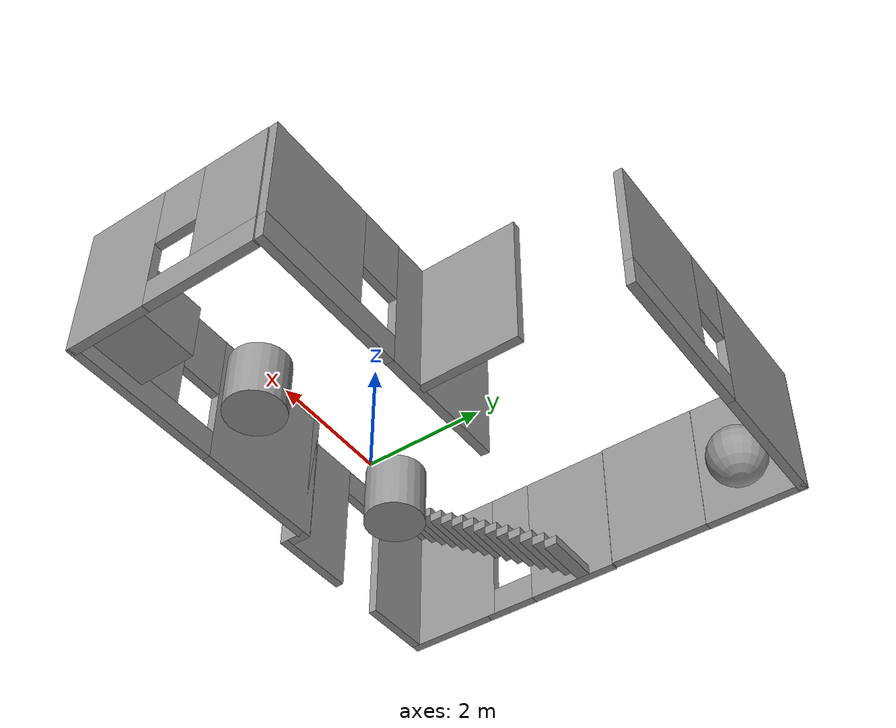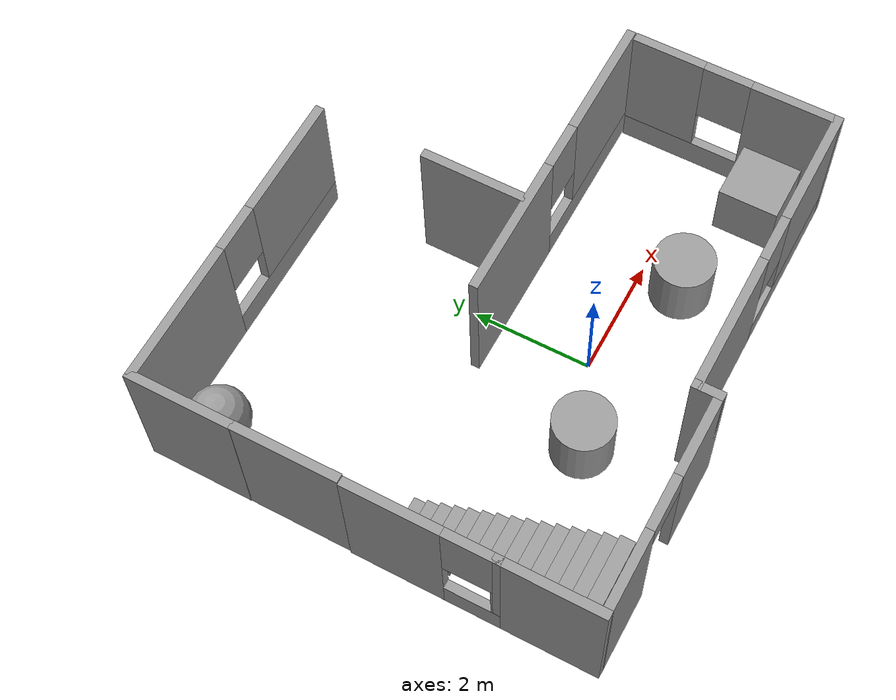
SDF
<?xml version='1.0'?>
<sdf version='1.7'>
  <model name='housing'>
    <link name='Stairs_2'>
      <self_collide>0</self_collide>
      <enable_wind>0</enable_wind>
      <kinematic>0</kinematic>
      <pose>0 0 0 0 -0 0</pose>
      <visual name='Stairs_2_Visual_0'>
        <pose>-3.77414 1.15965 0.083333 0 -0 0</pose>
        <geometry>
          <box>
            <size>1 0.233333 0.166667</size>
          </box>
        </geometry>
        <material>
          <script>
            <uri>file://media/materials/scripts/gazebo.material</uri>
            <name>Gazebo/Grey</name>
          </script>
          <ambient>1 1 1 1</ambient>
          <shader type='pixel'/>
        </material>
        <meta>
          <layer>0</layer>
        </meta>
        <transparency>0</transparency>
        <cast_shadows>1</cast_shadows>
      </visual>
      <visual name='Stairs_2_Visual_1'>
        <pose>-3.77414 0.926314 0.25 0 -0 0</pose>
        <geometry>
          <box>
            <size>1 0.233333 0.166667</size>
          </box>
        </geometry>
        <material>
          <script>
            <uri>file://media/materials/scripts/gazebo.material</uri>
            <name>Gazebo/Grey</name>
          </script>
          <ambient>1 1 1 1</ambient>
          <shader type='pixel'/>
        </material>
        <meta>
          <layer>0</layer>
        </meta>
        <transparency>0</transparency>
        <cast_shadows>1</cast_shadows>
      </visual>
      <visual name='Stairs_2_Visual_2'>
        <pose>-3.77414 0.692981 0.416667 0 -0 0</pose>
        <geometry>
          <box>
            <size>1 0.233333 0.166667</size>
          </box>
        </geometry>
        <material>
          <script>
            <uri>file://media/materials/scripts/gazebo.material</uri>
            <name>Gazebo/Grey</name>
          </script>
          <ambient>1 1 1 1</ambient>
          <shader type='pixel'/>
        </material>
        <meta>
          <layer>0</layer>
        </meta>
        <transparency>0</transparency>
        <cast_shadows>1</cast_shadows>
      </visual>
      <visual name='Stairs_2_Visual_3'>
        <pose>-3.77414 0.459648 0.583333 0 -0 0</pose>
        <geometry>
          <box>
            <size>1 0.233333 0.166667</size>
          </box>
        </geometry>
        <material>
          <script>
            <uri>file://media/materials/scripts/gazebo.material</uri>
            <name>Gazebo/Grey</name>
          </script>
          <ambient>1 1 1 1</ambient>
          <shader type='pixel'/>
        </material>
        <meta>
          <layer>0</layer>
        </meta>
        <transparency>0</transparency>
        <cast_shadows>1</cast_shadows>
      </visual>
      <visual name='Stairs_2_Visual_4'>
        <pose>-3.77414 0.226314 0.75 0 -0 0</pose>
        <geometry>
          <box>
            <size>1 0.233333 0.166667</size>
          </box>
        </geometry>
        <material>
          <script>
            <uri>file://media/materials/scripts/gazebo.material</uri>
            <name>Gazebo/Grey</name>
          </script>
          <ambient>1 1 1 1</ambient>
          <shader type='pixel'/>
        </material>
        <meta>
          <layer>0</layer>
        </meta>
        <transparency>0</transparency>
        <cast_shadows>1</cast_shadows>
      </visual>
      <visual name='Stairs_2_Visual_5'>
        <pose>-3.77414 -0.007019 0.916667 0 -0 0</pose>
        <geometry>
          <box>
            <size>1 0.233333 0.166667</size>
          </box>
        </geometry>
        <material>
          <script>
            <uri>file://media/materials/scripts/gazebo.material</uri>
            <name>Gazebo/Grey</name>
          </script>
          <ambient>1 1 1 1</ambient>
          <shader type='pixel'/>
        </material>
        <meta>
          <layer>0</layer>
        </meta>
        <transparency>0</transparency>
        <cast_shadows>1</cast_shadows>
      </visual>
      <visual name='Stairs_2_Visual_6'>
        <pose>-3.77414 -0.240352 1.08333 0 -0 0</pose>
        <geometry>
          <box>
            <size>1 0.233333 0.166667</size>
          </box>
        </geometry>
        <material>
          <script>
            <uri>file://media/materials/scripts/gazebo.material</uri>
            <name>Gazebo/Grey</name>
          </script>
          <ambient>1 1 1 1</ambient>
          <shader type='pixel'/>
        </material>
        <meta>
          <layer>0</layer>
        </meta>
        <transparency>0</transparency>
        <cast_shadows>1</cast_shadows>
      </visual>
      <visual name='Stairs_2_Visual_7'>
        <pose>-3.77414 -0.473686 1.25 0 -0 0</pose>
        <geometry>
          <box>
            <size>1 0.233333 0.166667</size>
          </box>
        </geometry>
        <material>
          <script>
            <uri>file://media/materials/scripts/gazebo.material</uri>
            <name>Gazebo/Grey</name>
          </script>
          <ambient>1 1 1 1</ambient>
          <shader type='pixel'/>
        </material>
        <meta>
          <layer>0</layer>
        </meta>
        <transparency>0</transparency>
        <cast_shadows>1</cast_shadows>
      </visual>
      <visual name='Stairs_2_Visual_8'>
        <pose>-3.77414 -0.707019 1.41667 0 -0 0</pose>
        <geometry>
          <box>
            <size>1 0.233333 0.166667</size>
          </box>
        </geometry>
        <material>
          <script>
            <uri>file://media/materials/scripts/gazebo.material</uri>
            <name>Gazebo/Grey</name>
          </script>
          <ambient>1 1 1 1</ambient>
          <shader type='pixel'/>
        </material>
        <meta>
          <layer>0</layer>
        </meta>
        <transparency>0</transparency>
        <cast_shadows>1</cast_shadows>
      </visual>
      <visual name='Stairs_2_Visual_9'>
        <pose>-3.77414 -0.940352 1.58333 0 -0 0</pose>
        <geometry>
          <box>
            <size>1 0.233333 0.166667</size>
          </box>
        </geometry>
        <material>
          <script>
            <uri>file://media/materials/scripts/gazebo.material</uri>
            <name>Gazebo/Grey</name>
          </script>
          <ambient>1 1 1 1</ambient>
          <shader type='pixel'/>
        </material>
        <meta>
          <layer>0</layer>
        </meta>
        <transparency>0</transparency>
        <cast_shadows>1</cast_shadows>
      </visual>
      <visual name='Stairs_2_Visual_10'>
        <pose>-3.77414 -1.17369 1.75 0 -0 0</pose>
        <geometry>
          <box>
            <size>1 0.233333 0.166667</size>
          </box>
        </geometry>
        <material>
          <script>
            <uri>file://media/materials/scripts/gazebo.material</uri>
            <name>Gazebo/Grey</name>
          </script>
          <ambient>1 1 1 1</ambient>
          <shader type='pixel'/>
        </material>
        <meta>
          <layer>0</layer>
        </meta>
        <transparency>0</transparency>
        <cast_shadows>1</cast_shadows>
      </visual>
      <visual name='Stairs_2_Visual_11'>
        <pose>-3.77414 -1.40702 1.91667 0 -0 0</pose>
        <geometry>
          <box>
            <size>1 0.233333 0.166667</size>
          </box>
        </geometry>
        <material>
          <script>
            <uri>file://media/materials/scripts/gazebo.material</uri>
            <name>Gazebo/Grey</name>
          </script>
          <ambient>1 1 1 1</ambient>
          <shader type='pixel'/>
        </material>
        <meta>
          <layer>0</layer>
        </meta>
        <transparency>0</transparency>
        <cast_shadows>1</cast_shadows>
      </visual>
      <visual name='Stairs_2_Visual_12'>
        <pose>-3.77414 -1.64035 2.08333 0 -0 0</pose>
        <geometry>
          <box>
            <size>1 0.233333 0.166667</size>
          </box>
        </geometry>
        <material>
          <script>
            <uri>file://media/materials/scripts/gazebo.material</uri>
            <name>Gazebo/Grey</name>
          </script>
          <ambient>1 1 1 1</ambient>
          <shader type='pixel'/>
        </material>
        <meta>
          <layer>0</layer>
        </meta>
        <transparency>0</transparency>
        <cast_shadows>1</cast_shadows>
      </visual>
      <visual name='Stairs_2_Visual_13'>
        <pose>-3.77414 -1.87369 2.25 0 -0 0</pose>
        <geometry>
          <box>
            <size>1 0.233333 0.166667</size>
          </box>
        </geometry>
        <material>
          <script>
            <uri>file://media/materials/scripts/gazebo.material</uri>
            <name>Gazebo/Grey</name>
          </script>
          <ambient>1 1 1 1</ambient>
          <shader type='pixel'/>
        </material>
        <meta>
          <layer>0</layer>
        </meta>
        <transparency>0</transparency>
        <cast_shadows>1</cast_shadows>
      </visual>
      <visual name='Stairs_2_Visual_14'>
        <pose>-3.77414 -2.10702 2.41667 0 -0 0</pose>
        <geometry>
          <box>
            <size>1 0.233333 0.166667</size>
          </box>
        </geometry>
        <material>
          <script>
            <uri>file://media/materials/scripts/gazebo.material</uri>
            <name>Gazebo/Grey</name>
          </script>
          <ambient>1 1 1 1</ambient>
          <shader type='pixel'/>
        </material>
        <meta>
          <layer>0</layer>
        </meta>
        <transparency>0</transparency>
        <cast_shadows>1</cast_shadows>
      </visual>
      <collision name='Stairs_2_Collision_0'>
        <laser_retro>0</laser_retro>
        <max_contacts>10</max_contacts>
        <pose>-3.77414 1.15965 0.083333 0 -0 0</pose>
        <geometry>
          <box>
            <size>1 0.233333 0.166667</size>
          </box>
        </geometry>
        <surface>
          <friction>
            <ode>
              <mu>1</mu>
              <mu2>1</mu2>
              <fdir1>0 0 0</fdir1>
              <slip1>0</slip1>
              <slip2>0</slip2>
            </ode>
            <torsional>
              <coefficient>1</coefficient>
              <patch_radius>0</patch_radius>
              <surface_radius>0</surface_radius>
              <use_patch_radius>1</use_patch_radius>
              <ode>
                <slip>0</slip>
              </ode>
            </torsional>
          </friction>
          <bounce>
            <restitution_coefficient>0</restitution_coefficient>
            <threshold>1e+06</threshold>
          </bounce>
          <contact>
            <collide_without_contact>0</collide_without_contact>
            <collide_without_contact_bitmask>1</collide_without_contact_bitmask>
            <collide_bitmask>1</collide_bitmask>
            <ode>
              <soft_cfm>0</soft_cfm>
              <soft_erp>0.2</soft_erp>
              <kp>1e+13</kp>
              <kd>1</kd>
              <max_vel>0.01</max_vel>
              <min_depth>0</min_depth>
            </ode>
            <bullet>
              <split_impulse>1</split_impulse>
              <split_impulse_penetration_threshold>-0.01</split_impulse_penetration_threshold>
              <soft_cfm>0</soft_cfm>
              <soft_erp>0.2</soft_erp>
              <kp>1e+13</kp>
              <kd>1</kd>
            </bullet>
          </contact>
        </surface>
      </collision>
      <collision name='Stairs_2_Collision_1'>
        <laser_retro>0</laser_retro>
        <max_contacts>10</max_contacts>
        <pose>-3.77414 0.926314 0.25 0 -0 0</pose>
        <geometry>
          <box>
            <size>1 0.233333 0.166667</size>
          </box>
        </geometry>
        <surface>
          <friction>
            <ode>
              <mu>1</mu>
              <mu2>1</mu2>
              <fdir1>0 0 0</fdir1>
              <slip1>0</slip1>
              <slip2>0</slip2>
            </ode>
            <torsional>
              <coefficient>1</coefficient>
              <patch_radius>0</patch_radius>
              <surface_radius>0</surface_radius>
              <use_patch_radius>1</use_patch_radius>
              <ode>
                <slip>0</slip>
              </ode>
            </torsional>
          </friction>
          <bounce>
            <restitution_coefficient>0</restitution_coefficient>
            <threshold>1e+06</threshold>
          </bounce>
          <contact>
            <collide_without_contact>0</collide_without_contact>
            <collide_without_contact_bitmask>1</collide_without_contact_bitmask>
            <collide_bitmask>1</collide_bitmask>
            <ode>
              <soft_cfm>0</soft_cfm>
              <soft_erp>0.2</soft_erp>
              <kp>1e+13</kp>
              <kd>1</kd>
              <max_vel>0.01</max_vel>
              <min_depth>0</min_depth>
            </ode>
            <bullet>
              <split_impulse>1</split_impulse>
              <split_impulse_penetration_threshold>-0.01</split_impulse_penetration_threshold>
              <soft_cfm>0</soft_cfm>
              <soft_erp>0.2</soft_erp>
              <kp>1e+13</kp>
              <kd>1</kd>
            </bullet>
          </contact>
        </surface>
      </collision>
      <collision name='Stairs_2_Collision_2'>
        <laser_retro>0</laser_retro>
        <max_contacts>10</max_contacts>
        <pose>-3.77414 0.692981 0.416667 0 -0 0</pose>
        <geometry>
          <box>
            <size>1 0.233333 0.166667</size>
          </box>
        </geometry>
        <surface>
          <friction>
            <ode>
              <mu>1</mu>
              <mu2>1</mu2>
              <fdir1>0 0 0</fdir1>
              <slip1>0</slip1>
              <slip2>0</slip2>
            </ode>
            <torsional>
              <coefficient>1</coefficient>
              <patch_radius>0</patch_radius>
              <surface_radius>0</surface_radius>
              <use_patch_radius>1</use_patch_radius>
              <ode>
                <slip>0</slip>
              </ode>
            </torsional>
          </friction>
          <bounce>
            <restitution_coefficient>0</restitution_coefficient>
            <threshold>1e+06</threshold>
          </bounce>
          <contact>
            <collide_without_contact>0</collide_without_contact>
            <collide_without_contact_bitmask>1</collide_without_contact_bitmask>
            <collide_bitmask>1</collide_bitmask>
            <ode>
              <soft_cfm>0</soft_cfm>
              <soft_erp>0.2</soft_erp>
              <kp>1e+13</kp>
              <kd>1</kd>
              <max_vel>0.01</max_vel>
              <min_depth>0</min_depth>
            </ode>
            <bullet>
              <split_impulse>1</split_impulse>
              <split_impulse_penetration_threshold>-0.01</split_impulse_penetration_threshold>
              <soft_cfm>0</soft_cfm>
              <soft_erp>0.2</soft_erp>
              <kp>1e+13</kp>
              <kd>1</kd>
            </bullet>
          </contact>
        </surface>
      </collision>
      <collision name='Stairs_2_Collision_3'>
        <laser_retro>0</laser_retro>
        <max_contacts>10</max_contacts>
        <pose>-3.77414 0.459648 0.583333 0 -0 0</pose>
        <geometry>
          <box>
            <size>1 0.233333 0.166667</size>
          </box>
        </geometry>
        <surface>
          <friction>
            <ode>
              <mu>1</mu>
              <mu2>1</mu2>
              <fdir1>0 0 0</fdir1>
              <slip1>0</slip1>
              <slip2>0</slip2>
            </ode>
            <torsional>
              <coefficient>1</coefficient>
              <patch_radius>0</patch_radius>
              <surface_radius>0</surface_radius>
              <use_patch_radius>1</use_patch_radius>
              <ode>
                <slip>0</slip>
              </ode>
            </torsional>
          </friction>
          <bounce>
            <restitution_coefficient>0</restitution_coefficient>
            <threshold>1e+06</threshold>
          </bounce>
          <contact>
            <collide_without_contact>0</collide_without_contact>
            <collide_without_contact_bitmask>1</collide_without_contact_bitmask>
            <collide_bitmask>1</collide_bitmask>
            <ode>
              <soft_cfm>0</soft_cfm>
              <soft_erp>0.2</soft_erp>
              <kp>1e+13</kp>
              <kd>1</kd>
              <max_vel>0.01</max_vel>
              <min_depth>0</min_depth>
            </ode>
            <bullet>
              <split_impulse>1</split_impulse>
              <split_impulse_penetration_threshold>-0.01</split_impulse_penetration_threshold>
              <soft_cfm>0</soft_cfm>
              <soft_erp>0.2</soft_erp>
              <kp>1e+13</kp>
              <kd>1</kd>
            </bullet>
          </contact>
        </surface>
      </collision>
      <collision name='Stairs_2_Collision_4'>
        <laser_retro>0</laser_retro>
        <max_contacts>10</max_contacts>
        <pose>-3.77414 0.226314 0.75 0 -0 0</pose>
        <geometry>
          <box>
            <size>1 0.233333 0.166667</size>
          </box>
        </geometry>
        <surface>
          <friction>
            <ode>
              <mu>1</mu>
              <mu2>1</mu2>
              <fdir1>0 0 0</fdir1>
              <slip1>0</slip1>
              <slip2>0</slip2>
            </ode>
            <torsional>
              <coefficient>1</coefficient>
              <patch_radius>0</patch_radius>
              <surface_radius>0</surface_radius>
              <use_patch_radius>1</use_patch_radius>
              <ode>
                <slip>0</slip>
              </ode>
            </torsional>
          </friction>
          <bounce>
            <restitution_coefficient>0</restitution_coefficient>
            <threshold>1e+06</threshold>
          </bounce>
          <contact>
            <collide_without_contact>0</collide_without_contact>
            <collide_without_contact_bitmask>1</collide_without_contact_bitmask>
            <collide_bitmask>1</collide_bitmask>
            <ode>
              <soft_cfm>0</soft_cfm>
              <soft_erp>0.2</soft_erp>
              <kp>1e+13</kp>
              <kd>1</kd>
              <max_vel>0.01</max_vel>
              <min_depth>0</min_depth>
            </ode>
            <bullet>
              <split_impulse>1</split_impulse>
              <split_impulse_penetration_threshold>-0.01</split_impulse_penetration_threshold>
              <soft_cfm>0</soft_cfm>
              <soft_erp>0.2</soft_erp>
              <kp>1e+13</kp>
              <kd>1</kd>
            </bullet>
          </contact>
        </surface>
      </collision>
      <collision name='Stairs_2_Collision_5'>
        <laser_retro>0</laser_retro>
        <max_contacts>10</max_contacts>
        <pose>-3.77414 -0.007019 0.916667 0 -0 0</pose>
        <geometry>
          <box>
            <size>1 0.233333 0.166667</size>
          </box>
        </geometry>
        <surface>
          <friction>
            <ode>
              <mu>1</mu>
              <mu2>1</mu2>
              <fdir1>0 0 0</fdir1>
              <slip1>0</slip1>
              <slip2>0</slip2>
            </ode>
            <torsional>
              <coefficient>1</coefficient>
              <patch_radius>0</patch_radius>
              <surface_radius>0</surface_radius>
              <use_patch_radius>1</use_patch_radius>
              <ode>
                <slip>0</slip>
              </ode>
            </torsional>
          </friction>
          <bounce>
            <restitution_coefficient>0</restitution_coefficient>
            <threshold>1e+06</threshold>
          </bounce>
          <contact>
            <collide_without_contact>0</collide_without_contact>
            <collide_without_contact_bitmask>1</collide_without_contact_bitmask>
            <collide_bitmask>1</collide_bitmask>
            <ode>
              <soft_cfm>0</soft_cfm>
              <soft_erp>0.2</soft_erp>
              <kp>1e+13</kp>
              <kd>1</kd>
              <max_vel>0.01</max_vel>
              <min_depth>0</min_depth>
            </ode>
            <bullet>
              <split_impulse>1</split_impulse>
              <split_impulse_penetration_threshold>-0.01</split_impulse_penetration_threshold>
              <soft_cfm>0</soft_cfm>
              <soft_erp>0.2</soft_erp>
              <kp>1e+13</kp>
              <kd>1</kd>
            </bullet>
          </contact>
        </surface>
      </collision>
      <collision name='Stairs_2_Collision_6'>
        <laser_retro>0</laser_retro>
        <max_contacts>10</max_contacts>
        <pose>-3.77414 -0.240352 1.08333 0 -0 0</pose>
        <geometry>
          <box>
            <size>1 0.233333 0.166667</size>
          </box>
        </geometry>
        <surface>
          <friction>
            <ode>
              <mu>1</mu>
              <mu2>1</mu2>
              <fdir1>0 0 0</fdir1>
              <slip1>0</slip1>
              <slip2>0</slip2>
            </ode>
            <torsional>
              <coefficient>1</coefficient>
              <patch_radius>0</patch_radius>
              <surface_radius>0</surface_radius>
              <use_patch_radius>1</use_patch_radius>
              <ode>
                <slip>0</slip>
              </ode>
            </torsional>
          </friction>
          <bounce>
            <restitution_coefficient>0</restitution_coefficient>
            <threshold>1e+06</threshold>
          </bounce>
          <contact>
            <collide_without_contact>0</collide_without_contact>
            <collide_without_contact_bitmask>1</collide_without_contact_bitmask>
            <collide_bitmask>1</collide_bitmask>
            <ode>
              <soft_cfm>0</soft_cfm>
              <soft_erp>0.2</soft_erp>
              <kp>1e+13</kp>
              <kd>1</kd>
              <max_vel>0.01</max_vel>
              <min_depth>0</min_depth>
            </ode>
            <bullet>
              <split_impulse>1</split_impulse>
              <split_impulse_penetration_threshold>-0.01</split_impulse_penetration_threshold>
              <soft_cfm>0</soft_cfm>
              <soft_erp>0.2</soft_erp>
              <kp>1e+13</kp>
              <kd>1</kd>
            </bullet>
          </contact>
        </surface>
      </collision>
      <collision name='Stairs_2_Collision_7'>
        <laser_retro>0</laser_retro>
        <max_contacts>10</max_contacts>
        <pose>-3.77414 -0.473686 1.25 0 -0 0</pose>
        <geometry>
          <box>
            <size>1 0.233333 0.166667</size>
          </box>
        </geometry>
        <surface>
          <friction>
            <ode>
              <mu>1</mu>
              <mu2>1</mu2>
              <fdir1>0 0 0</fdir1>
              <slip1>0</slip1>
              <slip2>0</slip2>
            </ode>
            <torsional>
              <coefficient>1</coefficient>
              <patch_radius>0</patch_radius>
              <surface_radius>0</surface_radius>
              <use_patch_radius>1</use_patch_radius>
              <ode>
                <slip>0</slip>
              </ode>
            </torsional>
          </friction>
          <bounce>
            <restitution_coefficient>0</restitution_coefficient>
            <threshold>1e+06</threshold>
          </bounce>
          <contact>
            <collide_without_contact>0</collide_without_contact>
            <collide_without_contact_bitmask>1</collide_without_contact_bitmask>
            <collide_bitmask>1</collide_bitmask>
            <ode>
              <soft_cfm>0</soft_cfm>
              <soft_erp>0.2</soft_erp>
              <kp>1e+13</kp>
              <kd>1</kd>
              <max_vel>0.01</max_vel>
              <min_depth>0</min_depth>
            </ode>
            <bullet>
              <split_impulse>1</split_impulse>
              <split_impulse_penetration_threshold>-0.01</split_impulse_penetration_threshold>
              <soft_cfm>0</soft_cfm>
              <soft_erp>0.2</soft_erp>
              <kp>1e+13</kp>
              <kd>1</kd>
            </bullet>
          </contact>
        </surface>
      </collision>
      <collision name='Stairs_2_Collision_8'>
        <laser_retro>0</laser_retro>
        <max_contacts>10</max_contacts>
        <pose>-3.77414 -0.707019 1.41667 0 -0 0</pose>
        <geometry>
          <box>
            <size>1 0.233333 0.166667</size>
          </box>
        </geometry>
        <surface>
          <friction>
            <ode>
              <mu>1</mu>
              <mu2>1</mu2>
              <fdir1>0 0 0</fdir1>
              <slip1>0</slip1>
              <slip2>0</slip2>
            </ode>
            <torsional>
              <coefficient>1</coefficient>
              <patch_radius>0</patch_radius>
              <surface_radius>0</surface_radius>
              <use_patch_radius>1</use_patch_radius>
              <ode>
                <slip>0</slip>
              </ode>
            </torsional>
          </friction>
          <bounce>
            <restitution_coefficient>0</restitution_coefficient>
            <threshold>1e+06</threshold>
          </bounce>
          <contact>
            <collide_without_contact>0</collide_without_contact>
            <collide_without_contact_bitmask>1</collide_without_contact_bitmask>
            <collide_bitmask>1</collide_bitmask>
            <ode>
              <soft_cfm>0</soft_cfm>
              <soft_erp>0.2</soft_erp>
              <kp>1e+13</kp>
              <kd>1</kd>
              <max_vel>0.01</max_vel>
              <min_depth>0</min_depth>
            </ode>
            <bullet>
              <split_impulse>1</split_impulse>
              <split_impulse_penetration_threshold>-0.01</split_impulse_penetration_threshold>
              <soft_cfm>0</soft_cfm>
              <soft_erp>0.2</soft_erp>
              <kp>1e+13</kp>
              <kd>1</kd>
            </bullet>
          </contact>
        </surface>
      </collision>
      <collision name='Stairs_2_Collision_9'>
        <laser_retro>0</laser_retro>
        <max_contacts>10</max_contacts>
        <pose>-3.77414 -0.940352 1.58333 0 -0 0</pose>
        <geometry>
          <box>
            <size>1 0.233333 0.166667</size>
          </box>
        </geometry>
        <surface>
          <friction>
            <ode>
              <mu>1</mu>
              <mu2>1</mu2>
              <fdir1>0 0 0</fdir1>
              <slip1>0</slip1>
              <slip2>0</slip2>
            </ode>
            <torsional>
              <coefficient>1</coefficient>
              <patch_radius>0</patch_radius>
              <surface_radius>0</surface_radius>
              <use_patch_radius>1</use_patch_radius>
              <ode>
                <slip>0</slip>
              </ode>
            </torsional>
          </friction>
          <bounce>
            <restitution_coefficient>0</restitution_coefficient>
            <threshold>1e+06</threshold>
          </bounce>
          <contact>
            <collide_without_contact>0</collide_without_contact>
            <collide_without_contact_bitmask>1</collide_without_contact_bitmask>
            <collide_bitmask>1</collide_bitmask>
            <ode>
              <soft_cfm>0</soft_cfm>
              <soft_erp>0.2</soft_erp>
              <kp>1e+13</kp>
              <kd>1</kd>
              <max_vel>0.01</max_vel>
              <min_depth>0</min_depth>
            </ode>
            <bullet>
              <split_impulse>1</split_impulse>
              <split_impulse_penetration_threshold>-0.01</split_impulse_penetration_threshold>
              <soft_cfm>0</soft_cfm>
              <soft_erp>0.2</soft_erp>
              <kp>1e+13</kp>
              <kd>1</kd>
            </bullet>
          </contact>
        </surface>
      </collision>
      <collision name='Stairs_2_Collision_10'>
        <laser_retro>0</laser_retro>
        <max_contacts>10</max_contacts>
        <pose>-3.77414 -1.17369 1.75 0 -0 0</pose>
        <geometry>
          <box>
            <size>1 0.233333 0.166667</size>
          </box>
        </geometry>
        <surface>
          <friction>
            <ode>
              <mu>1</mu>
              <mu2>1</mu2>
              <fdir1>0 0 0</fdir1>
              <slip1>0</slip1>
              <slip2>0</slip2>
            </ode>
            <torsional>
              <coefficient>1</coefficient>
              <patch_radius>0</patch_radius>
              <surface_radius>0</surface_radius>
              <use_patch_radius>1</use_patch_radius>
              <ode>
                <slip>0</slip>
              </ode>
            </torsional>
          </friction>
          <bounce>
            <restitution_coefficient>0</restitution_coefficient>
            <threshold>1e+06</threshold>
          </bounce>
          <contact>
            <collide_without_contact>0</collide_without_contact>
            <collide_without_contact_bitmask>1</collide_without_contact_bitmask>
            <collide_bitmask>1</collide_bitmask>
            <ode>
              <soft_cfm>0</soft_cfm>
              <soft_erp>0.2</soft_erp>
              <kp>1e+13</kp>
              <kd>1</kd>
              <max_vel>0.01</max_vel>
              <min_depth>0</min_depth>
            </ode>
            <bullet>
              <split_impulse>1</split_impulse>
              <split_impulse_penetration_threshold>-0.01</split_impulse_penetration_threshold>
              <soft_cfm>0</soft_cfm>
              <soft_erp>0.2</soft_erp>
              <kp>1e+13</kp>
              <kd>1</kd>
            </bullet>
          </contact>
        </surface>
      </collision>
      <collision name='Stairs_2_Collision_11'>
        <laser_retro>0</laser_retro>
        <max_contacts>10</max_contacts>
        <pose>-3.77414 -1.40702 1.91667 0 -0 0</pose>
        <geometry>
          <box>
            <size>1 0.233333 0.166667</size>
          </box>
        </geometry>
        <surface>
          <friction>
            <ode>
              <mu>1</mu>
              <mu2>1</mu2>
              <fdir1>0 0 0</fdir1>
              <slip1>0</slip1>
              <slip2>0</slip2>
            </ode>
            <torsional>
              <coefficient>1</coefficient>
              <patch_radius>0</patch_radius>
              <surface_radius>0</surface_radius>
              <use_patch_radius>1</use_patch_radius>
              <ode>
                <slip>0</slip>
              </ode>
            </torsional>
          </friction>
          <bounce>
            <restitution_coefficient>0</restitution_coefficient>
            <threshold>1e+06</threshold>
          </bounce>
          <contact>
            <collide_without_contact>0</collide_without_contact>
            <collide_without_contact_bitmask>1</collide_without_contact_bitmask>
            <collide_bitmask>1</collide_bitmask>
            <ode>
              <soft_cfm>0</soft_cfm>
              <soft_erp>0.2</soft_erp>
              <kp>1e+13</kp>
              <kd>1</kd>
              <max_vel>0.01</max_vel>
              <min_depth>0</min_depth>
            </ode>
            <bullet>
              <split_impulse>1</split_impulse>
              <split_impulse_penetration_threshold>-0.01</split_impulse_penetration_threshold>
              <soft_cfm>0</soft_cfm>
              <soft_erp>0.2</soft_erp>
              <kp>1e+13</kp>
              <kd>1</kd>
            </bullet>
          </contact>
        </surface>
      </collision>
      <collision name='Stairs_2_Collision_12'>
        <laser_retro>0</laser_retro>
        <max_contacts>10</max_contacts>
        <pose>-3.77414 -1.64035 2.08333 0 -0 0</pose>
        <geometry>
          <box>
            <size>1 0.233333 0.166667</size>
          </box>
        </geometry>
        <surface>
          <friction>
            <ode>
              <mu>1</mu>
              <mu2>1</mu2>
              <fdir1>0 0 0</fdir1>
              <slip1>0</slip1>
              <slip2>0</slip2>
            </ode>
            <torsional>
              <coefficient>1</coefficient>
              <patch_radius>0</patch_radius>
              <surface_radius>0</surface_radius>
              <use_patch_radius>1</use_patch_radius>
              <ode>
                <slip>0</slip>
              </ode>
            </torsional>
          </friction>
          <bounce>
            <restitution_coefficient>0</restitution_coefficient>
            <threshold>1e+06</threshold>
          </bounce>
          <contact>
            <collide_without_contact>0</collide_without_contact>
            <collide_without_contact_bitmask>1</collide_without_contact_bitmask>
            <collide_bitmask>1</collide_bitmask>
            <ode>
              <soft_cfm>0</soft_cfm>
              <soft_erp>0.2</soft_erp>
              <kp>1e+13</kp>
              <kd>1</kd>
              <max_vel>0.01</max_vel>
              <min_depth>0</min_depth>
            </ode>
            <bullet>
              <split_impulse>1</split_impulse>
              <split_impulse_penetration_threshold>-0.01</split_impulse_penetration_threshold>
              <soft_cfm>0</soft_cfm>
              <soft_erp>0.2</soft_erp>
              <kp>1e+13</kp>
              <kd>1</kd>
            </bullet>
          </contact>
        </surface>
      </collision>
      <collision name='Stairs_2_Collision_13'>
        <laser_retro>0</laser_retro>
        <max_contacts>10</max_contacts>
        <pose>-3.77414 -1.87369 2.25 0 -0 0</pose>
        <geometry>
          <box>
            <size>1 0.233333 0.166667</size>
          </box>
        </geometry>
        <surface>
          <friction>
            <ode>
              <mu>1</mu>
              <mu2>1</mu2>
              <fdir1>0 0 0</fdir1>
              <slip1>0</slip1>
              <slip2>0</slip2>
            </ode>
            <torsional>
              <coefficient>1</coefficient>
              <patch_radius>0</patch_radius>
              <surface_radius>0</surface_radius>
              <use_patch_radius>1</use_patch_radius>
              <ode>
                <slip>0</slip>
              </ode>
            </torsional>
          </friction>
          <bounce>
            <restitution_coefficient>0</restitution_coefficient>
            <threshold>1e+06</threshold>
          </bounce>
          <contact>
            <collide_without_contact>0</collide_without_contact>
            <collide_without_contact_bitmask>1</collide_without_contact_bitmask>
            <collide_bitmask>1</collide_bitmask>
            <ode>
              <soft_cfm>0</soft_cfm>
              <soft_erp>0.2</soft_erp>
              <kp>1e+13</kp>
              <kd>1</kd>
              <max_vel>0.01</max_vel>
              <min_depth>0</min_depth>
            </ode>
            <bullet>
              <split_impulse>1</split_impulse>
              <split_impulse_penetration_threshold>-0.01</split_impulse_penetration_threshold>
              <soft_cfm>0</soft_cfm>
              <soft_erp>0.2</soft_erp>
              <kp>1e+13</kp>
              <kd>1</kd>
            </bullet>
          </contact>
        </surface>
      </collision>
      <collision name='Stairs_2_Collision_14'>
        <laser_retro>0</laser_retro>
        <max_contacts>10</max_contacts>
        <pose>-3.77414 -2.10702 2.41667 0 -0 0</pose>
        <geometry>
          <box>
            <size>1 0.233333 0.166667</size>
          </box>
        </geometry>
        <surface>
          <friction>
            <ode>
              <mu>1</mu>
              <mu2>1</mu2>
              <fdir1>0 0 0</fdir1>
              <slip1>0</slip1>
              <slip2>0</slip2>
            </ode>
            <torsional>
              <coefficient>1</coefficient>
              <patch_radius>0</patch_radius>
              <surface_radius>0</surface_radius>
              <use_patch_radius>1</use_patch_radius>
              <ode>
                <slip>0</slip>
              </ode>
            </torsional>
          </friction>
          <bounce>
            <restitution_coefficient>0</restitution_coefficient>
            <threshold>1e+06</threshold>
          </bounce>
          <contact>
            <collide_without_contact>0</collide_without_contact>
            <collide_without_contact_bitmask>1</collide_without_contact_bitmask>
            <collide_bitmask>1</collide_bitmask>
            <ode>
              <soft_cfm>0</soft_cfm>
              <soft_erp>0.2</soft_erp>
              <kp>1e+13</kp>
              <kd>1</kd>
              <max_vel>0.01</max_vel>
              <min_depth>0</min_depth>
            </ode>
            <bullet>
              <split_impulse>1</split_impulse>
              <split_impulse_penetration_threshold>-0.01</split_impulse_penetration_threshold>
              <soft_cfm>0</soft_cfm>
              <soft_erp>0.2</soft_erp>
              <kp>1e+13</kp>
              <kd>1</kd>
            </bullet>
          </contact>
        </surface>
      </collision>
    </link>
    <link name='Wall_28'>
      <pose>-4.35 0.469647 0 0 0 -1.5708</pose>
      <self_collide>0</self_collide>
      <enable_wind>0</enable_wind>
      <kinematic>0</kinematic>
      <visual name='Wall_28_Visual_0'>
        <pose>-0.459531 0 1.25 0 -0 0</pose>
        <geometry>
          <box>
            <size>1.58094 0.15 2.5</size>
          </box>
        </geometry>
        <material>
          <script>
            <uri>file://media/materials/scripts/gazebo.material</uri>
            <name>Gazebo/Grey</name>
          </script>
          <ambient>1 1 1 1</ambient>
          <shader type='pixel'/>
        </material>
        <meta>
          <layer>0</layer>
        </meta>
        <transparency>0</transparency>
        <cast_shadows>1</cast_shadows>
      </visual>
      <visual name='Wall_28_Visual_1'>
        <pose>0.790469 0 0.25 0 -0 0</pose>
        <geometry>
          <box>
            <size>0.919061 0.15 0.5</size>
          </box>
        </geometry>
        <material>
          <script>
            <uri>file://media/materials/scripts/gazebo.material</uri>
            <name>Gazebo/Grey</name>
          </script>
          <ambient>1 1 1 1</ambient>
          <shader type='pixel'/>
        </material>
        <meta>
          <layer>0</layer>
        </meta>
        <transparency>0</transparency>
        <cast_shadows>1</cast_shadows>
      </visual>
      <visual name='Wall_28_Visual_2'>
        <pose>1.19047 0 1.5 0 -0 0</pose>
        <geometry>
          <box>
            <size>0.119061 0.15 2</size>
          </box>
        </geometry>
        <material>
          <script>
            <uri>file://media/materials/scripts/gazebo.material</uri>
            <name>Gazebo/Grey</name>
          </script>
          <ambient>1 1 1 1</ambient>
          <shader type='pixel'/>
        </material>
        <meta>
          <layer>0</layer>
        </meta>
        <transparency>0</transparency>
        <cast_shadows>1</cast_shadows>
      </visual>
      <visual name='Wall_28_Visual_3'>
        <pose>0.730939 0 1.9 0 -0 0</pose>
        <geometry>
          <box>
            <size>0.8 0.15 1.2</size>
          </box>
        </geometry>
        <material>
          <script>
            <uri>file://media/materials/scripts/gazebo.material</uri>
            <name>Gazebo/Grey</name>
          </script>
          <ambient>1 1 1 1</ambient>
          <shader type='pixel'/>
        </material>
        <meta>
          <layer>0</layer>
        </meta>
        <transparency>0</transparency>
        <cast_shadows>1</cast_shadows>
      </visual>
      <collision name='Wall_28_Collision_0'>
        <laser_retro>0</laser_retro>
        <max_contacts>10</max_contacts>
        <pose>-0.459531 0 1.25 0 -0 0</pose>
        <geometry>
          <box>
            <size>1.58094 0.15 2.5</size>
          </box>
        </geometry>
        <surface>
          <friction>
            <ode>
              <mu>1</mu>
              <mu2>1</mu2>
              <fdir1>0 0 0</fdir1>
              <slip1>0</slip1>
              <slip2>0</slip2>
            </ode>
            <torsional>
              <coefficient>1</coefficient>
              <patch_radius>0</patch_radius>
              <surface_radius>0</surface_radius>
              <use_patch_radius>1</use_patch_radius>
              <ode>
                <slip>0</slip>
              </ode>
            </torsional>
          </friction>
          <bounce>
            <restitution_coefficient>0</restitution_coefficient>
            <threshold>1e+06</threshold>
          </bounce>
          <contact>
            <collide_without_contact>0</collide_without_contact>
            <collide_without_contact_bitmask>1</collide_without_contact_bitmask>
            <collide_bitmask>1</collide_bitmask>
            <ode>
              <soft_cfm>0</soft_cfm>
              <soft_erp>0.2</soft_erp>
              <kp>1e+13</kp>
              <kd>1</kd>
              <max_vel>0.01</max_vel>
              <min_depth>0</min_depth>
            </ode>
            <bullet>
              <split_impulse>1</split_impulse>
              <split_impulse_penetration_threshold>-0.01</split_impulse_penetration_threshold>
              <soft_cfm>0</soft_cfm>
              <soft_erp>0.2</soft_erp>
              <kp>1e+13</kp>
              <kd>1</kd>
            </bullet>
          </contact>
        </surface>
      </collision>
      <collision name='Wall_28_Collision_1'>
        <laser_retro>0</laser_retro>
        <max_contacts>10</max_contacts>
        <pose>0.790469 0 0.25 0 -0 0</pose>
        <geometry>
          <box>
            <size>0.919061 0.15 0.5</size>
          </box>
        </geometry>
        <surface>
          <friction>
            <ode>
              <mu>1</mu>
              <mu2>1</mu2>
              <fdir1>0 0 0</fdir1>
              <slip1>0</slip1>
              <slip2>0</slip2>
            </ode>
            <torsional>
              <coefficient>1</coefficient>
              <patch_radius>0</patch_radius>
              <surface_radius>0</surface_radius>
              <use_patch_radius>1</use_patch_radius>
              <ode>
                <slip>0</slip>
              </ode>
            </torsional>
          </friction>
          <bounce>
            <restitution_coefficient>0</restitution_coefficient>
            <threshold>1e+06</threshold>
          </bounce>
          <contact>
            <collide_without_contact>0</collide_without_contact>
            <collide_without_contact_bitmask>1</collide_without_contact_bitmask>
            <collide_bitmask>1</collide_bitmask>
            <ode>
              <soft_cfm>0</soft_cfm>
              <soft_erp>0.2</soft_erp>
              <kp>1e+13</kp>
              <kd>1</kd>
              <max_vel>0.01</max_vel>
              <min_depth>0</min_depth>
            </ode>
            <bullet>
              <split_impulse>1</split_impulse>
              <split_impulse_penetration_threshold>-0.01</split_impulse_penetration_threshold>
              <soft_cfm>0</soft_cfm>
              <soft_erp>0.2</soft_erp>
              <kp>1e+13</kp>
              <kd>1</kd>
            </bullet>
          </contact>
        </surface>
      </collision>
      <collision name='Wall_28_Collision_2'>
        <laser_retro>0</laser_retro>
        <max_contacts>10</max_contacts>
        <pose>1.19047 0 1.5 0 -0 0</pose>
        <geometry>
          <box>
            <size>0.119061 0.15 2</size>
          </box>
        </geometry>
        <surface>
          <friction>
            <ode>
              <mu>1</mu>
              <mu2>1</mu2>
              <fdir1>0 0 0</fdir1>
              <slip1>0</slip1>
              <slip2>0</slip2>
            </ode>
            <torsional>
              <coefficient>1</coefficient>
              <patch_radius>0</patch_radius>
              <surface_radius>0</surface_radius>
              <use_patch_radius>1</use_patch_radius>
              <ode>
                <slip>0</slip>
              </ode>
            </torsional>
          </friction>
          <bounce>
            <restitution_coefficient>0</restitution_coefficient>
            <threshold>1e+06</threshold>
          </bounce>
          <contact>
            <collide_without_contact>0</collide_without_contact>
            <collide_without_contact_bitmask>1</collide_without_contact_bitmask>
            <collide_bitmask>1</collide_bitmask>
            <ode>
              <soft_cfm>0</soft_cfm>
              <soft_erp>0.2</soft_erp>
              <kp>1e+13</kp>
              <kd>1</kd>
              <max_vel>0.01</max_vel>
              <min_depth>0</min_depth>
            </ode>
            <bullet>
              <split_impulse>1</split_impulse>
              <split_impulse_penetration_threshold>-0.01</split_impulse_penetration_threshold>
              <soft_cfm>0</soft_cfm>
              <soft_erp>0.2</soft_erp>
              <kp>1e+13</kp>
              <kd>1</kd>
            </bullet>
          </contact>
        </surface>
      </collision>
      <collision name='Wall_28_Collision_3'>
        <laser_retro>0</laser_retro>
        <max_contacts>10</max_contacts>
        <pose>0.730939 0 1.9 0 -0 0</pose>
        <geometry>
          <box>
            <size>0.8 0.15 1.2</size>
          </box>
        </geometry>
        <surface>
          <friction>
            <ode>
              <mu>1</mu>
              <mu2>1</mu2>
              <fdir1>0 0 0</fdir1>
              <slip1>0</slip1>
              <slip2>0</slip2>
            </ode>
            <torsional>
              <coefficient>1</coefficient>
              <patch_radius>0</patch_radius>
              <surface_radius>0</surface_radius>
              <use_patch_radius>1</use_patch_radius>
              <ode>
                <slip>0</slip>
              </ode>
            </torsional>
          </friction>
          <bounce>
            <restitution_coefficient>0</restitution_coefficient>
            <threshold>1e+06</threshold>
          </bounce>
          <contact>
            <collide_without_contact>0</collide_without_contact>
            <collide_without_contact_bitmask>1</collide_without_contact_bitmask>
            <collide_bitmask>1</collide_bitmask>
            <ode>
              <soft_cfm>0</soft_cfm>
              <soft_erp>0.2</soft_erp>
              <kp>1e+13</kp>
              <kd>1</kd>
              <max_vel>0.01</max_vel>
              <min_depth>0</min_depth>
            </ode>
            <bullet>
              <split_impulse>1</split_impulse>
              <split_impulse_penetration_threshold>-0.01</split_impulse_penetration_threshold>
              <soft_cfm>0</soft_cfm>
              <soft_erp>0.2</soft_erp>
              <kp>1e+13</kp>
              <kd>1</kd>
            </bullet>
          </contact>
        </surface>
      </collision>
    </link>
    <link name='Wall_51'>
      <pose>-4.35 -1.50535 0 0 0 -1.5708</pose>
      <self_collide>0</self_collide>
      <enable_wind>0</enable_wind>
      <kinematic>0</kinematic>
      <visual name='Wall_51_Visual'>
        <pose>0 0 1.25 0 -0 0</pose>
        <geometry>
          <box>
            <size>1.75 0.15 2.5</size>
          </box>
        </geometry>
        <material>
          <script>
            <uri>file://media/materials/scripts/gazebo.material</uri>
            <name>Gazebo/Grey</name>
          </script>
          <ambient>1 1 1 1</ambient>
          <shader type='pixel'/>
        </material>
        <meta>
          <layer>0</layer>
        </meta>
        <transparency>0</transparency>
        <cast_shadows>1</cast_shadows>
      </visual>
      <collision name='Wall_51_Collision'>
        <laser_retro>0</laser_retro>
        <max_contacts>10</max_contacts>
        <pose>0 0 1.25 0 -0 0</pose>
        <geometry>
          <box>
            <size>1.75 0.15 2.5</size>
          </box>
        </geometry>
        <surface>
          <friction>
            <ode>
              <mu>1</mu>
              <mu2>1</mu2>
              <fdir1>0 0 0</fdir1>
              <slip1>0</slip1>
              <slip2>0</slip2>
            </ode>
            <torsional>
              <coefficient>1</coefficient>
              <patch_radius>0</patch_radius>
              <surface_radius>0</surface_radius>
              <use_patch_radius>1</use_patch_radius>
              <ode>
                <slip>0</slip>
              </ode>
            </torsional>
          </friction>
          <bounce>
            <restitution_coefficient>0</restitution_coefficient>
            <threshold>1e+06</threshold>
          </bounce>
          <contact>
            <collide_without_contact>0</collide_without_contact>
            <collide_without_contact_bitmask>1</collide_without_contact_bitmask>
            <collide_bitmask>1</collide_bitmask>
            <ode>
              <soft_cfm>0</soft_cfm>
              <soft_erp>0.2</soft_erp>
              <kp>1e+13</kp>
              <kd>1</kd>
              <max_vel>0.01</max_vel>
              <min_depth>0</min_depth>
            </ode>
            <bullet>
              <split_impulse>1</split_impulse>
              <split_impulse_penetration_threshold>-0.01</split_impulse_penetration_threshold>
              <soft_cfm>0</soft_cfm>
              <soft_erp>0.2</soft_erp>
              <kp>1e+13</kp>
              <kd>1</kd>
            </bullet>
          </contact>
        </surface>
      </collision>
    </link>
    <link name='Wall_51_clone'>
      <pose>-4.32868 2.60917 0 0 0 -1.5708</pose>
      <self_collide>0</self_collide>
      <enable_wind>0</enable_wind>
      <kinematic>0</kinematic>
      <visual name='Wall_51_Visual'>
        <pose>0 0 1.25 0 -0 0</pose>
        <geometry>
          <box>
            <size>1.75 0.15 2.5</size>
          </box>
        </geometry>
        <material>
          <script>
            <uri>file://media/materials/scripts/gazebo.material</uri>
            <name>Gazebo/Grey</name>
          </script>
          <ambient>1 1 1 1</ambient>
          <shader type='pixel'/>
        </material>
        <meta>
          <layer>0</layer>
        </meta>
        <transparency>0</transparency>
        <cast_shadows>1</cast_shadows>
      </visual>
      <collision name='Wall_51_Collision'>
        <laser_retro>0</laser_retro>
        <max_contacts>10</max_contacts>
        <pose>0 0 1.25 0 -0 0</pose>
        <geometry>
          <box>
            <size>1.75 0.15 2.5</size>
          </box>
        </geometry>
        <surface>
          <friction>
            <ode>
              <mu>1</mu>
              <mu2>1</mu2>
              <fdir1>0 0 0</fdir1>
              <slip1>0</slip1>
              <slip2>0</slip2>
            </ode>
            <torsional>
              <coefficient>1</coefficient>
              <patch_radius>0</patch_radius>
              <surface_radius>0</surface_radius>
              <use_patch_radius>1</use_patch_radius>
              <ode>
                <slip>0</slip>
              </ode>
            </torsional>
          </friction>
          <bounce>
            <restitution_coefficient>0</restitution_coefficient>
            <threshold>1e+06</threshold>
          </bounce>
          <contact>
            <collide_without_contact>0</collide_without_contact>
            <collide_without_contact_bitmask>1</collide_without_contact_bitmask>
            <collide_bitmask>1</collide_bitmask>
            <ode>
              <soft_cfm>0</soft_cfm>
              <soft_erp>0.2</soft_erp>
              <kp>1e+13</kp>
              <kd>1</kd>
              <max_vel>0.01</max_vel>
              <min_depth>0</min_depth>
            </ode>
            <bullet>
              <split_impulse>1</split_impulse>
              <split_impulse_penetration_threshold>-0.01</split_impulse_penetration_threshold>
              <soft_cfm>0</soft_cfm>
              <soft_erp>0.2</soft_erp>
              <kp>1e+13</kp>
              <kd>1</kd>
            </bullet>
          </contact>
        </surface>
      </collision>
    </link>
    <link name='Wall_51_clone_clone'>
      <pose>-4.33427 4.33509 0 0 0 -1.5708</pose>
      <self_collide>0</self_collide>
      <enable_wind>0</enable_wind>
      <kinematic>0</kinematic>
      <visual name='Wall_51_Visual'>
        <pose>0 0 1.25 0 -0 0</pose>
        <geometry>
          <box>
            <size>1.75 0.15 2.5</size>
          </box>
        </geometry>
        <material>
          <script>
            <uri>file://media/materials/scripts/gazebo.material</uri>
            <name>Gazebo/Grey</name>
          </script>
          <ambient>1 1 1 1</ambient>
          <shader type='pixel'/>
        </material>
        <meta>
          <layer>0</layer>
        </meta>
        <transparency>0</transparency>
        <cast_shadows>1</cast_shadows>
      </visual>
      <collision name='Wall_51_Collision'>
        <laser_retro>0</laser_retro>
        <max_contacts>10</max_contacts>
        <pose>0 0 1.25 0 -0 0</pose>
        <geometry>
          <box>
            <size>1.75 0.15 2.5</size>
          </box>
        </geometry>
        <surface>
          <friction>
            <ode>
              <mu>1</mu>
              <mu2>1</mu2>
              <fdir1>0 0 0</fdir1>
              <slip1>0</slip1>
              <slip2>0</slip2>
            </ode>
            <torsional>
              <coefficient>1</coefficient>
              <patch_radius>0</patch_radius>
              <surface_radius>0</surface_radius>
              <use_patch_radius>1</use_patch_radius>
              <ode>
                <slip>0</slip>
              </ode>
            </torsional>
          </friction>
          <bounce>
            <restitution_coefficient>0</restitution_coefficient>
            <threshold>1e+06</threshold>
          </bounce>
          <contact>
            <collide_without_contact>0</collide_without_contact>
            <collide_without_contact_bitmask>1</collide_without_contact_bitmask>
            <collide_bitmask>1</collide_bitmask>
            <ode>
              <soft_cfm>0</soft_cfm>
              <soft_erp>0.2</soft_erp>
              <kp>1e+13</kp>
              <kd>1</kd>
              <max_vel>0.01</max_vel>
              <min_depth>0</min_depth>
            </ode>
            <bullet>
              <split_impulse>1</split_impulse>
              <split_impulse_penetration_threshold>-0.01</split_impulse_penetration_threshold>
              <soft_cfm>0</soft_cfm>
              <soft_erp>0.2</soft_erp>
              <kp>1e+13</kp>
              <kd>1</kd>
            </bullet>
          </contact>
        </surface>
      </collision>
    </link>
    <link name='Wall_51_clone_clone_clone'>
      <pose>0.871259 2.47337 0 0 0 -1.5708</pose>
      <self_collide>0</self_collide>
      <enable_wind>0</enable_wind>
      <kinematic>0</kinematic>
      <visual name='Wall_51_Visual'>
        <pose>0 0 1.25 0 -0 0</pose>
        <geometry>
          <box>
            <size>1.75 0.15 2.5</size>
          </box>
        </geometry>
        <material>
          <script>
            <uri>file://media/materials/scripts/gazebo.material</uri>
            <name>Gazebo/Grey</name>
          </script>
          <ambient>1 1 1 1</ambient>
          <shader type='pixel'/>
        </material>
        <meta>
          <layer>0</layer>
        </meta>
        <transparency>0</transparency>
        <cast_shadows>1</cast_shadows>
      </visual>
      <collision name='Wall_51_Collision'>
        <laser_retro>0</laser_retro>
        <max_contacts>10</max_contacts>
        <pose>0 0 1.25 0 -0 0</pose>
        <geometry>
          <box>
            <size>1.75 0.15 2.5</size>
          </box>
        </geometry>
        <surface>
          <friction>
            <ode>
              <mu>1</mu>
              <mu2>1</mu2>
              <fdir1>0 0 0</fdir1>
              <slip1>0</slip1>
              <slip2>0</slip2>
            </ode>
            <torsional>
              <coefficient>1</coefficient>
              <patch_radius>0</patch_radius>
              <surface_radius>0</surface_radius>
              <use_patch_radius>1</use_patch_radius>
              <ode>
                <slip>0</slip>
              </ode>
            </torsional>
          </friction>
          <bounce>
            <restitution_coefficient>0</restitution_coefficient>
            <threshold>1e+06</threshold>
          </bounce>
          <contact>
            <collide_without_contact>0</collide_without_contact>
            <collide_without_contact_bitmask>1</collide_without_contact_bitmask>
            <collide_bitmask>1</collide_bitmask>
            <ode>
              <soft_cfm>0</soft_cfm>
              <soft_erp>0.2</soft_erp>
              <kp>1e+13</kp>
              <kd>1</kd>
              <max_vel>0.01</max_vel>
              <min_depth>0</min_depth>
            </ode>
            <bullet>
              <split_impulse>1</split_impulse>
              <split_impulse_penetration_threshold>-0.01</split_impulse_penetration_threshold>
              <soft_cfm>0</soft_cfm>
              <soft_erp>0.2</soft_erp>
              <kp>1e+13</kp>
              <kd>1</kd>
            </bullet>
          </contact>
        </surface>
      </collision>
    </link>
    <link name='Wall_52'>
      <pose>-2.55 -2.30535 0 0 -0 0</pose>
      <self_collide>0</self_collide>
      <enable_wind>0</enable_wind>
      <kinematic>0</kinematic>
      <visual name='Wall_52_Visual_0'>
        <pose>-1.17213 0 1.25 0 -0 0</pose>
        <geometry>
          <box>
            <size>1.40574 0.15 2.5</size>
          </box>
        </geometry>
        <material>
          <script>
            <uri>file://media/materials/scripts/gazebo.material</uri>
            <name>Gazebo/Grey</name>
          </script>
          <ambient>1 1 1 1</ambient>
          <shader type='pixel'/>
        </material>
        <meta>
          <layer>0</layer>
        </meta>
        <transparency>0</transparency>
        <cast_shadows>1</cast_shadows>
      </visual>
      <visual name='Wall_52_Visual_1'>
        <pose>1.15287 0 1.25 0 -0 0</pose>
        <geometry>
          <box>
            <size>1.44426 0.15 2.5</size>
          </box>
        </geometry>
        <material>
          <script>
            <uri>file://media/materials/scripts/gazebo.material</uri>
            <name>Gazebo/Grey</name>
          </script>
          <ambient>1 1 1 1</ambient>
          <shader type='pixel'/>
        </material>
        <meta>
          <layer>0</layer>
        </meta>
        <transparency>0</transparency>
        <cast_shadows>1</cast_shadows>
      </visual>
      <visual name='Wall_52_Visual_2'>
        <pose>-0.019263 0 2.25 0 -0 0</pose>
        <geometry>
          <box>
            <size>0.9 0.15 0.5</size>
          </box>
        </geometry>
        <material>
          <script>
            <uri>file://media/materials/scripts/gazebo.material</uri>
            <name>Gazebo/Grey</name>
          </script>
          <ambient>1 1 1 1</ambient>
          <shader type='pixel'/>
        </material>
        <meta>
          <layer>0</layer>
        </meta>
        <transparency>0</transparency>
        <cast_shadows>1</cast_shadows>
      </visual>
      <collision name='Wall_52_Collision_0'>
        <laser_retro>0</laser_retro>
        <max_contacts>10</max_contacts>
        <pose>-1.17213 0 1.25 0 -0 0</pose>
        <geometry>
          <box>
            <size>1.40574 0.15 2.5</size>
          </box>
        </geometry>
        <surface>
          <friction>
            <ode>
              <mu>1</mu>
              <mu2>1</mu2>
              <fdir1>0 0 0</fdir1>
              <slip1>0</slip1>
              <slip2>0</slip2>
            </ode>
            <torsional>
              <coefficient>1</coefficient>
              <patch_radius>0</patch_radius>
              <surface_radius>0</surface_radius>
              <use_patch_radius>1</use_patch_radius>
              <ode>
                <slip>0</slip>
              </ode>
            </torsional>
          </friction>
          <bounce>
            <restitution_coefficient>0</restitution_coefficient>
            <threshold>1e+06</threshold>
          </bounce>
          <contact>
            <collide_without_contact>0</collide_without_contact>
            <collide_without_contact_bitmask>1</collide_without_contact_bitmask>
            <collide_bitmask>1</collide_bitmask>
            <ode>
              <soft_cfm>0</soft_cfm>
              <soft_erp>0.2</soft_erp>
              <kp>1e+13</kp>
              <kd>1</kd>
              <max_vel>0.01</max_vel>
              <min_depth>0</min_depth>
            </ode>
            <bullet>
              <split_impulse>1</split_impulse>
              <split_impulse_penetration_threshold>-0.01</split_impulse_penetration_threshold>
              <soft_cfm>0</soft_cfm>
              <soft_erp>0.2</soft_erp>
              <kp>1e+13</kp>
              <kd>1</kd>
            </bullet>
          </contact>
        </surface>
      </collision>
      <collision name='Wall_52_Collision_2'>
        <laser_retro>0</laser_retro>
        <max_contacts>10</max_contacts>
        <pose>-0.019263 0 2.25 0 -0 0</pose>
        <geometry>
          <box>
            <size>0.9 0.15 0.5</size>
          </box>
        </geometry>
        <surface>
          <friction>
            <ode>
              <mu>1</mu>
              <mu2>1</mu2>
              <fdir1>0 0 0</fdir1>
              <slip1>0</slip1>
              <slip2>0</slip2>
            </ode>
            <torsional>
              <coefficient>1</coefficient>
              <patch_radius>0</patch_radius>
              <surface_radius>0</surface_radius>
              <use_patch_radius>1</use_patch_radius>
              <ode>
                <slip>0</slip>
              </ode>
            </torsional>
          </friction>
          <bounce>
            <restitution_coefficient>0</restitution_coefficient>
            <threshold>1e+06</threshold>
          </bounce>
          <contact>
            <collide_without_contact>0</collide_without_contact>
            <collide_without_contact_bitmask>1</collide_without_contact_bitmask>
            <collide_bitmask>1</collide_bitmask>
            <ode>
              <soft_cfm>0</soft_cfm>
              <soft_erp>0.2</soft_erp>
              <kp>1e+13</kp>
              <kd>1</kd>
              <max_vel>0.01</max_vel>
              <min_depth>0</min_depth>
            </ode>
            <bullet>
              <split_impulse>1</split_impulse>
              <split_impulse_penetration_threshold>-0.01</split_impulse_penetration_threshold>
              <soft_cfm>0</soft_cfm>
              <soft_erp>0.2</soft_erp>
              <kp>1e+13</kp>
              <kd>1</kd>
            </bullet>
          </contact>
        </surface>
      </collision>
      <collision name='Wall_52_Collision_1'>
        <laser_retro>0</laser_retro>
        <max_contacts>10</max_contacts>
        <pose>1.15287 0 1.25 0 -0 0</pose>
        <geometry>
          <box>
            <size>1.44426 0.15 2.5</size>
          </box>
        </geometry>
        <surface>
          <friction>
            <ode>
              <mu>1</mu>
              <mu2>1</mu2>
              <fdir1>0 0 0</fdir1>
              <slip1>0</slip1>
              <slip2>0</slip2>
            </ode>
            <torsional>
              <coefficient>1</coefficient>
              <patch_radius>0</patch_radius>
              <surface_radius>0</surface_radius>
              <use_patch_radius>1</use_patch_radius>
              <ode>
                <slip>0</slip>
              </ode>
            </torsional>
          </friction>
          <bounce>
            <restitution_coefficient>0</restitution_coefficient>
            <threshold>1e+06</threshold>
          </bounce>
          <contact>
            <collide_without_contact>0</collide_without_contact>
            <collide_without_contact_bitmask>1</collide_without_contact_bitmask>
            <collide_bitmask>1</collide_bitmask>
            <ode>
              <soft_cfm>0</soft_cfm>
              <soft_erp>0.2</soft_erp>
              <kp>1e+13</kp>
              <kd>1</kd>
              <max_vel>0.01</max_vel>
              <min_depth>0</min_depth>
            </ode>
            <bullet>
              <split_impulse>1</split_impulse>
              <split_impulse_penetration_threshold>-0.01</split_impulse_penetration_threshold>
              <soft_cfm>0</soft_cfm>
              <soft_erp>0.2</soft_erp>
              <kp>1e+13</kp>
              <kd>1</kd>
            </bullet>
          </contact>
        </surface>
      </collision>
    </link>
    <link name='Wall_53'>
      <pose>-0.75 -2.13035 0 0 -0 1.5708</pose>
      <self_collide>0</self_collide>
      <enable_wind>0</enable_wind>
      <kinematic>0</kinematic>
      <visual name='Wall_53_Visual'>
        <pose>0 0 1.25 0 -0 0</pose>
        <geometry>
          <box>
            <size>0.5 0.15 2.5</size>
          </box>
        </geometry>
        <material>
          <script>
            <uri>file://media/materials/scripts/gazebo.material</uri>
            <name>Gazebo/Grey</name>
          </script>
          <ambient>1 1 1 1</ambient>
          <shader type='pixel'/>
        </material>
        <meta>
          <layer>0</layer>
        </meta>
        <transparency>0</transparency>
        <cast_shadows>1</cast_shadows>
      </visual>
      <collision name='Wall_53_Collision'>
        <laser_retro>0</laser_retro>
        <max_contacts>10</max_contacts>
        <pose>0 0 1.25 0 -0 0</pose>
        <geometry>
          <box>
            <size>0.5 0.15 2.5</size>
          </box>
        </geometry>
        <surface>
          <friction>
            <ode>
              <mu>1</mu>
              <mu2>1</mu2>
              <fdir1>0 0 0</fdir1>
              <slip1>0</slip1>
              <slip2>0</slip2>
            </ode>
            <torsional>
              <coefficient>1</coefficient>
              <patch_radius>0</patch_radius>
              <surface_radius>0</surface_radius>
              <use_patch_radius>1</use_patch_radius>
              <ode>
                <slip>0</slip>
              </ode>
            </torsional>
          </friction>
          <bounce>
            <restitution_coefficient>0</restitution_coefficient>
            <threshold>1e+06</threshold>
          </bounce>
          <contact>
            <collide_without_contact>0</collide_without_contact>
            <collide_without_contact_bitmask>1</collide_without_contact_bitmask>
            <collide_bitmask>1</collide_bitmask>
            <ode>
              <soft_cfm>0</soft_cfm>
              <soft_erp>0.2</soft_erp>
              <kp>1e+13</kp>
              <kd>1</kd>
              <max_vel>0.01</max_vel>
              <min_depth>0</min_depth>
            </ode>
            <bullet>
              <split_impulse>1</split_impulse>
              <split_impulse_penetration_threshold>-0.01</split_impulse_penetration_threshold>
              <soft_cfm>0</soft_cfm>
              <soft_erp>0.2</soft_erp>
              <kp>1e+13</kp>
              <kd>1</kd>
            </bullet>
          </contact>
        </surface>
      </collision>
    </link>
    <link name='Wall_54'>
      <pose>1.8 -1.95535 0 0 -0 0</pose>
      <self_collide>0</self_collide>
      <enable_wind>0</enable_wind>
      <kinematic>0</kinematic>
      <visual name='Wall_54_Visual_0'>
        <pose>-1.42713 0 1.25 0 -0 0</pose>
        <geometry>
          <box>
            <size>2.39574 0.15 2.5</size>
          </box>
        </geometry>
        <material>
          <script>
            <uri>file://media/materials/scripts/gazebo.material</uri>
            <name>Gazebo/Grey</name>
          </script>
          <ambient>1 1 1 1</ambient>
          <shader type='pixel'/>
        </material>
        <meta>
          <layer>0</layer>
        </meta>
        <transparency>0</transparency>
        <cast_shadows>1</cast_shadows>
      </visual>
      <visual name='Wall_54_Visual_1'>
        <pose>1.19787 0 0.25 0 -0 0</pose>
        <geometry>
          <box>
            <size>2.85426 0.15 0.5</size>
          </box>
        </geometry>
        <material>
          <script>
            <uri>file://media/materials/scripts/gazebo.material</uri>
            <name>Gazebo/Grey</name>
          </script>
          <ambient>1 1 1 1</ambient>
          <shader type='pixel'/>
        </material>
        <meta>
          <layer>0</layer>
        </meta>
        <transparency>0</transparency>
        <cast_shadows>1</cast_shadows>
      </visual>
      <visual name='Wall_54_Visual_2'>
        <pose>1.59787 0 1.5 0 -0 0</pose>
        <geometry>
          <box>
            <size>2.05426 0.15 2</size>
          </box>
        </geometry>
        <material>
          <script>
            <uri>file://media/materials/scripts/gazebo.material</uri>
            <name>Gazebo/Grey</name>
          </script>
          <ambient>1 1 1 1</ambient>
          <shader type='pixel'/>
        </material>
        <meta>
          <layer>0</layer>
        </meta>
        <transparency>0</transparency>
        <cast_shadows>1</cast_shadows>
      </visual>
      <visual name='Wall_54_Visual_3'>
        <pose>0.170737 0 1.9 0 -0 0</pose>
        <geometry>
          <box>
            <size>0.8 0.15 1.2</size>
          </box>
        </geometry>
        <material>
          <script>
            <uri>file://media/materials/scripts/gazebo.material</uri>
            <name>Gazebo/Grey</name>
          </script>
          <ambient>1 1 1 1</ambient>
          <shader type='pixel'/>
        </material>
        <meta>
          <layer>0</layer>
        </meta>
        <transparency>0</transparency>
        <cast_shadows>1</cast_shadows>
      </visual>
      <collision name='Wall_54_Collision_0'>
        <laser_retro>0</laser_retro>
        <max_contacts>10</max_contacts>
        <pose>-1.42713 0 1.25 0 -0 0</pose>
        <geometry>
          <box>
            <size>2.39574 0.15 2.5</size>
          </box>
        </geometry>
        <surface>
          <friction>
            <ode>
              <mu>1</mu>
              <mu2>1</mu2>
              <fdir1>0 0 0</fdir1>
              <slip1>0</slip1>
              <slip2>0</slip2>
            </ode>
            <torsional>
              <coefficient>1</coefficient>
              <patch_radius>0</patch_radius>
              <surface_radius>0</surface_radius>
              <use_patch_radius>1</use_patch_radius>
              <ode>
                <slip>0</slip>
              </ode>
            </torsional>
          </friction>
          <bounce>
            <restitution_coefficient>0</restitution_coefficient>
            <threshold>1e+06</threshold>
          </bounce>
          <contact>
            <collide_without_contact>0</collide_without_contact>
            <collide_without_contact_bitmask>1</collide_without_contact_bitmask>
            <collide_bitmask>1</collide_bitmask>
            <ode>
              <soft_cfm>0</soft_cfm>
              <soft_erp>0.2</soft_erp>
              <kp>1e+13</kp>
              <kd>1</kd>
              <max_vel>0.01</max_vel>
              <min_depth>0</min_depth>
            </ode>
            <bullet>
              <split_impulse>1</split_impulse>
              <split_impulse_penetration_threshold>-0.01</split_impulse_penetration_threshold>
              <soft_cfm>0</soft_cfm>
              <soft_erp>0.2</soft_erp>
              <kp>1e+13</kp>
              <kd>1</kd>
            </bullet>
          </contact>
        </surface>
      </collision>
      <collision name='Wall_54_Collision_1'>
        <laser_retro>0</laser_retro>
        <max_contacts>10</max_contacts>
        <pose>1.19787 0 0.25 0 -0 0</pose>
        <geometry>
          <box>
            <size>2.85426 0.15 0.5</size>
          </box>
        </geometry>
        <surface>
          <friction>
            <ode>
              <mu>1</mu>
              <mu2>1</mu2>
              <fdir1>0 0 0</fdir1>
              <slip1>0</slip1>
              <slip2>0</slip2>
            </ode>
            <torsional>
              <coefficient>1</coefficient>
              <patch_radius>0</patch_radius>
              <surface_radius>0</surface_radius>
              <use_patch_radius>1</use_patch_radius>
              <ode>
                <slip>0</slip>
              </ode>
            </torsional>
          </friction>
          <bounce>
            <restitution_coefficient>0</restitution_coefficient>
            <threshold>1e+06</threshold>
          </bounce>
          <contact>
            <collide_without_contact>0</collide_without_contact>
            <collide_without_contact_bitmask>1</collide_without_contact_bitmask>
            <collide_bitmask>1</collide_bitmask>
            <ode>
              <soft_cfm>0</soft_cfm>
              <soft_erp>0.2</soft_erp>
              <kp>1e+13</kp>
              <kd>1</kd>
              <max_vel>0.01</max_vel>
              <min_depth>0</min_depth>
            </ode>
            <bullet>
              <split_impulse>1</split_impulse>
              <split_impulse_penetration_threshold>-0.01</split_impulse_penetration_threshold>
              <soft_cfm>0</soft_cfm>
              <soft_erp>0.2</soft_erp>
              <kp>1e+13</kp>
              <kd>1</kd>
            </bullet>
          </contact>
        </surface>
      </collision>
      <collision name='Wall_54_Collision_2'>
        <laser_retro>0</laser_retro>
        <max_contacts>10</max_contacts>
        <pose>1.59787 0 1.5 0 -0 0</pose>
        <geometry>
          <box>
            <size>2.05426 0.15 2</size>
          </box>
        </geometry>
        <surface>
          <friction>
            <ode>
              <mu>1</mu>
              <mu2>1</mu2>
              <fdir1>0 0 0</fdir1>
              <slip1>0</slip1>
              <slip2>0</slip2>
            </ode>
            <torsional>
              <coefficient>1</coefficient>
              <patch_radius>0</patch_radius>
              <surface_radius>0</surface_radius>
              <use_patch_radius>1</use_patch_radius>
              <ode>
                <slip>0</slip>
              </ode>
            </torsional>
          </friction>
          <bounce>
            <restitution_coefficient>0</restitution_coefficient>
            <threshold>1e+06</threshold>
          </bounce>
          <contact>
            <collide_without_contact>0</collide_without_contact>
            <collide_without_contact_bitmask>1</collide_without_contact_bitmask>
            <collide_bitmask>1</collide_bitmask>
            <ode>
              <soft_cfm>0</soft_cfm>
              <soft_erp>0.2</soft_erp>
              <kp>1e+13</kp>
              <kd>1</kd>
              <max_vel>0.01</max_vel>
              <min_depth>0</min_depth>
            </ode>
            <bullet>
              <split_impulse>1</split_impulse>
              <split_impulse_penetration_threshold>-0.01</split_impulse_penetration_threshold>
              <soft_cfm>0</soft_cfm>
              <soft_erp>0.2</soft_erp>
              <kp>1e+13</kp>
              <kd>1</kd>
            </bullet>
          </contact>
        </surface>
      </collision>
      <collision name='Wall_54_Collision_3'>
        <laser_retro>0</laser_retro>
        <max_contacts>10</max_contacts>
        <pose>0.170737 0 1.9 0 -0 0</pose>
        <geometry>
          <box>
            <size>0.8 0.15 1.2</size>
          </box>
        </geometry>
        <surface>
          <friction>
            <ode>
              <mu>1</mu>
              <mu2>1</mu2>
              <fdir1>0 0 0</fdir1>
              <slip1>0</slip1>
              <slip2>0</slip2>
            </ode>
            <torsional>
              <coefficient>1</coefficient>
              <patch_radius>0</patch_radius>
              <surface_radius>0</surface_radius>
              <use_patch_radius>1</use_patch_radius>
              <ode>
                <slip>0</slip>
              </ode>
            </torsional>
          </friction>
          <bounce>
            <restitution_coefficient>0</restitution_coefficient>
            <threshold>1e+06</threshold>
          </bounce>
          <contact>
            <collide_without_contact>0</collide_without_contact>
            <collide_without_contact_bitmask>1</collide_without_contact_bitmask>
            <collide_bitmask>1</collide_bitmask>
            <ode>
              <soft_cfm>0</soft_cfm>
              <soft_erp>0.2</soft_erp>
              <kp>1e+13</kp>
              <kd>1</kd>
              <max_vel>0.01</max_vel>
              <min_depth>0</min_depth>
            </ode>
            <bullet>
              <split_impulse>1</split_impulse>
              <split_impulse_penetration_threshold>-0.01</split_impulse_penetration_threshold>
              <soft_cfm>0</soft_cfm>
              <soft_erp>0.2</soft_erp>
              <kp>1e+13</kp>
              <kd>1</kd>
            </bullet>
          </contact>
        </surface>
      </collision>
    </link>
    <link name='Wall_54_clone'>
      <pose>-1.75776 5.13683 0 0 -0 0</pose>
      <self_collide>0</self_collide>
      <enable_wind>0</enable_wind>
      <kinematic>0</kinematic>
      <visual name='Wall_54_Visual_2'>
        <pose>1.59787 0 1.5 0 -0 0</pose>
        <geometry>
          <box>
            <size>2.05426 0.15 2</size>
          </box>
        </geometry>
        <material>
          <script>
            <uri>file://media/materials/scripts/gazebo.material</uri>
            <name>Gazebo/Grey</name>
          </script>
          <ambient>1 1 1 1</ambient>
          <shader type='pixel'/>
        </material>
        <meta>
          <layer>0</layer>
        </meta>
        <transparency>0</transparency>
        <cast_shadows>1</cast_shadows>
      </visual>
      <visual name='Wall_54_Visual_1'>
        <pose>1.19787 0 0.25 0 -0 0</pose>
        <geometry>
          <box>
            <size>2.85426 0.15 0.5</size>
          </box>
        </geometry>
        <material>
          <script>
            <uri>file://media/materials/scripts/gazebo.material</uri>
            <name>Gazebo/Grey</name>
          </script>
          <ambient>1 1 1 1</ambient>
          <shader type='pixel'/>
        </material>
        <meta>
          <layer>0</layer>
        </meta>
        <transparency>0</transparency>
        <cast_shadows>1</cast_shadows>
      </visual>
      <visual name='Wall_54_Visual_0'>
        <pose>-1.42713 0 1.25 0 -0 0</pose>
        <geometry>
          <box>
            <size>2.39574 0.15 2.5</size>
          </box>
        </geometry>
        <material>
          <script>
            <uri>file://media/materials/scripts/gazebo.material</uri>
            <name>Gazebo/Grey</name>
          </script>
          <ambient>1 1 1 1</ambient>
          <shader type='pixel'/>
        </material>
        <meta>
          <layer>0</layer>
        </meta>
        <transparency>0</transparency>
        <cast_shadows>1</cast_shadows>
      </visual>
      <visual name='Wall_54_Visual_3'>
        <pose>0.170737 0 1.9 0 -0 0</pose>
        <geometry>
          <box>
            <size>0.8 0.15 1.2</size>
          </box>
        </geometry>
        <material>
          <script>
            <uri>file://media/materials/scripts/gazebo.material</uri>
            <name>Gazebo/Grey</name>
          </script>
          <ambient>1 1 1 1</ambient>
          <shader type='pixel'/>
        </material>
        <meta>
          <layer>0</layer>
        </meta>
        <transparency>0</transparency>
        <cast_shadows>1</cast_shadows>
      </visual>
      <collision name='Wall_54_Collision_2'>
        <laser_retro>0</laser_retro>
        <max_contacts>10</max_contacts>
        <pose>1.59787 0 1.5 0 -0 0</pose>
        <geometry>
          <box>
            <size>2.05426 0.15 2</size>
          </box>
        </geometry>
        <surface>
          <friction>
            <ode>
              <mu>1</mu>
              <mu2>1</mu2>
              <fdir1>0 0 0</fdir1>
              <slip1>0</slip1>
              <slip2>0</slip2>
            </ode>
            <torsional>
              <coefficient>1</coefficient>
              <patch_radius>0</patch_radius>
              <surface_radius>0</surface_radius>
              <use_patch_radius>1</use_patch_radius>
              <ode>
                <slip>0</slip>
              </ode>
            </torsional>
          </friction>
          <bounce>
            <restitution_coefficient>0</restitution_coefficient>
            <threshold>1e+06</threshold>
          </bounce>
          <contact>
            <collide_without_contact>0</collide_without_contact>
            <collide_without_contact_bitmask>1</collide_without_contact_bitmask>
            <collide_bitmask>1</collide_bitmask>
            <ode>
              <soft_cfm>0</soft_cfm>
              <soft_erp>0.2</soft_erp>
              <kp>1e+13</kp>
              <kd>1</kd>
              <max_vel>0.01</max_vel>
              <min_depth>0</min_depth>
            </ode>
            <bullet>
              <split_impulse>1</split_impulse>
              <split_impulse_penetration_threshold>-0.01</split_impulse_penetration_threshold>
              <soft_cfm>0</soft_cfm>
              <soft_erp>0.2</soft_erp>
              <kp>1e+13</kp>
              <kd>1</kd>
            </bullet>
          </contact>
        </surface>
      </collision>
      <collision name='Wall_54_Collision_3'>
        <laser_retro>0</laser_retro>
        <max_contacts>10</max_contacts>
        <pose>0.170737 0 1.9 0 -0 0</pose>
        <geometry>
          <box>
            <size>0.8 0.15 1.2</size>
          </box>
        </geometry>
        <surface>
          <friction>
            <ode>
              <mu>1</mu>
              <mu2>1</mu2>
              <fdir1>0 0 0</fdir1>
              <slip1>0</slip1>
              <slip2>0</slip2>
            </ode>
            <torsional>
              <coefficient>1</coefficient>
              <patch_radius>0</patch_radius>
              <surface_radius>0</surface_radius>
              <use_patch_radius>1</use_patch_radius>
              <ode>
                <slip>0</slip>
              </ode>
            </torsional>
          </friction>
          <bounce>
            <restitution_coefficient>0</restitution_coefficient>
            <threshold>1e+06</threshold>
          </bounce>
          <contact>
            <collide_without_contact>0</collide_without_contact>
            <collide_without_contact_bitmask>1</collide_without_contact_bitmask>
            <collide_bitmask>1</collide_bitmask>
            <ode>
              <soft_cfm>0</soft_cfm>
              <soft_erp>0.2</soft_erp>
              <kp>1e+13</kp>
              <kd>1</kd>
              <max_vel>0.01</max_vel>
              <min_depth>0</min_depth>
            </ode>
            <bullet>
              <split_impulse>1</split_impulse>
              <split_impulse_penetration_threshold>-0.01</split_impulse_penetration_threshold>
              <soft_cfm>0</soft_cfm>
              <soft_erp>0.2</soft_erp>
              <kp>1e+13</kp>
              <kd>1</kd>
            </bullet>
          </contact>
        </surface>
      </collision>
      <collision name='Wall_54_Collision_1'>
        <laser_retro>0</laser_retro>
        <max_contacts>10</max_contacts>
        <pose>1.19787 0 0.25 0 -0 0</pose>
        <geometry>
          <box>
            <size>2.85426 0.15 0.5</size>
          </box>
        </geometry>
        <surface>
          <friction>
            <ode>
              <mu>1</mu>
              <mu2>1</mu2>
              <fdir1>0 0 0</fdir1>
              <slip1>0</slip1>
              <slip2>0</slip2>
            </ode>
            <torsional>
              <coefficient>1</coefficient>
              <patch_radius>0</patch_radius>
              <surface_radius>0</surface_radius>
              <use_patch_radius>1</use_patch_radius>
              <ode>
                <slip>0</slip>
              </ode>
            </torsional>
          </friction>
          <bounce>
            <restitution_coefficient>0</restitution_coefficient>
            <threshold>1e+06</threshold>
          </bounce>
          <contact>
            <collide_without_contact>0</collide_without_contact>
            <collide_without_contact_bitmask>1</collide_without_contact_bitmask>
            <collide_bitmask>1</collide_bitmask>
            <ode>
              <soft_cfm>0</soft_cfm>
              <soft_erp>0.2</soft_erp>
              <kp>1e+13</kp>
              <kd>1</kd>
              <max_vel>0.01</max_vel>
              <min_depth>0</min_depth>
            </ode>
            <bullet>
              <split_impulse>1</split_impulse>
              <split_impulse_penetration_threshold>-0.01</split_impulse_penetration_threshold>
              <soft_cfm>0</soft_cfm>
              <soft_erp>0.2</soft_erp>
              <kp>1e+13</kp>
              <kd>1</kd>
            </bullet>
          </contact>
        </surface>
      </collision>
      <collision name='Wall_54_Collision_0'>
        <laser_retro>0</laser_retro>
        <max_contacts>10</max_contacts>
        <pose>-1.42713 0 1.25 0 -0 0</pose>
        <geometry>
          <box>
            <size>2.39574 0.15 2.5</size>
          </box>
        </geometry>
        <surface>
          <friction>
            <ode>
              <mu>1</mu>
              <mu2>1</mu2>
              <fdir1>0 0 0</fdir1>
              <slip1>0</slip1>
              <slip2>0</slip2>
            </ode>
            <torsional>
              <coefficient>1</coefficient>
              <patch_radius>0</patch_radius>
              <surface_radius>0</surface_radius>
              <use_patch_radius>1</use_patch_radius>
              <ode>
                <slip>0</slip>
              </ode>
            </torsional>
          </friction>
          <bounce>
            <restitution_coefficient>0</restitution_coefficient>
            <threshold>1e+06</threshold>
          </bounce>
          <contact>
            <collide_without_contact>0</collide_without_contact>
            <collide_without_contact_bitmask>1</collide_without_contact_bitmask>
            <collide_bitmask>1</collide_bitmask>
            <ode>
              <soft_cfm>0</soft_cfm>
              <soft_erp>0.2</soft_erp>
              <kp>1e+13</kp>
              <kd>1</kd>
              <max_vel>0.01</max_vel>
              <min_depth>0</min_depth>
            </ode>
            <bullet>
              <split_impulse>1</split_impulse>
              <split_impulse_penetration_threshold>-0.01</split_impulse_penetration_threshold>
              <soft_cfm>0</soft_cfm>
              <soft_erp>0.2</soft_erp>
              <kp>1e+13</kp>
              <kd>1</kd>
            </bullet>
          </contact>
        </surface>
      </collision>
    </link>
    <link name='Wall_54_clone_clone'>
      <pose>1.79438 1.5644 0 0 -0 0</pose>
      <self_collide>0</self_collide>
      <enable_wind>0</enable_wind>
      <kinematic>0</kinematic>
      <visual name='Wall_54_Visual_2'>
        <pose>1.59787 0 1.5 0 -0 0</pose>
        <geometry>
          <box>
            <size>2.05426 0.15 2</size>
          </box>
        </geometry>
        <material>
          <script>
            <uri>file://media/materials/scripts/gazebo.material</uri>
            <name>Gazebo/Grey</name>
          </script>
          <ambient>1 1 1 1</ambient>
          <shader type='pixel'/>
        </material>
        <meta>
          <layer>0</layer>
        </meta>
        <transparency>0</transparency>
        <cast_shadows>1</cast_shadows>
      </visual>
      <visual name='Wall_54_Visual_3'>
        <pose>0.170737 0 1.9 0 -0 0</pose>
        <geometry>
          <box>
            <size>0.8 0.15 1.2</size>
          </box>
        </geometry>
        <material>
          <script>
            <uri>file://media/materials/scripts/gazebo.material</uri>
            <name>Gazebo/Grey</name>
          </script>
          <ambient>1 1 1 1</ambient>
          <shader type='pixel'/>
        </material>
        <meta>
          <layer>0</layer>
        </meta>
        <transparency>0</transparency>
        <cast_shadows>1</cast_shadows>
      </visual>
      <visual name='Wall_54_Visual_1'>
        <pose>1.19787 0 0.25 0 -0 0</pose>
        <geometry>
          <box>
            <size>2.85426 0.15 0.5</size>
          </box>
        </geometry>
        <material>
          <script>
            <uri>file://media/materials/scripts/gazebo.material</uri>
            <name>Gazebo/Grey</name>
          </script>
          <ambient>1 1 1 1</ambient>
          <shader type='pixel'/>
        </material>
        <meta>
          <layer>0</layer>
        </meta>
        <transparency>0</transparency>
        <cast_shadows>1</cast_shadows>
      </visual>
      <visual name='Wall_54_Visual_0'>
        <pose>-1.42713 0 1.25 0 -0 0</pose>
        <geometry>
          <box>
            <size>2.39574 0.15 2.5</size>
          </box>
        </geometry>
        <material>
          <script>
            <uri>file://media/materials/scripts/gazebo.material</uri>
            <name>Gazebo/Grey</name>
          </script>
          <ambient>1 1 1 1</ambient>
          <shader type='pixel'/>
        </material>
        <meta>
          <layer>0</layer>
        </meta>
        <transparency>0</transparency>
        <cast_shadows>1</cast_shadows>
      </visual>
      <collision name='Wall_54_Collision_1'>
        <laser_retro>0</laser_retro>
        <max_contacts>10</max_contacts>
        <pose>1.19787 0 0.25 0 -0 0</pose>
        <geometry>
          <box>
            <size>2.85426 0.15 0.5</size>
          </box>
        </geometry>
        <surface>
          <friction>
            <ode>
              <mu>1</mu>
              <mu2>1</mu2>
              <fdir1>0 0 0</fdir1>
              <slip1>0</slip1>
              <slip2>0</slip2>
            </ode>
            <torsional>
              <coefficient>1</coefficient>
              <patch_radius>0</patch_radius>
              <surface_radius>0</surface_radius>
              <use_patch_radius>1</use_patch_radius>
              <ode>
                <slip>0</slip>
              </ode>
            </torsional>
          </friction>
          <bounce>
            <restitution_coefficient>0</restitution_coefficient>
            <threshold>1e+06</threshold>
          </bounce>
          <contact>
            <collide_without_contact>0</collide_without_contact>
            <collide_without_contact_bitmask>1</collide_without_contact_bitmask>
            <collide_bitmask>1</collide_bitmask>
            <ode>
              <soft_cfm>0</soft_cfm>
              <soft_erp>0.2</soft_erp>
              <kp>1e+13</kp>
              <kd>1</kd>
              <max_vel>0.01</max_vel>
              <min_depth>0</min_depth>
            </ode>
            <bullet>
              <split_impulse>1</split_impulse>
              <split_impulse_penetration_threshold>-0.01</split_impulse_penetration_threshold>
              <soft_cfm>0</soft_cfm>
              <soft_erp>0.2</soft_erp>
              <kp>1e+13</kp>
              <kd>1</kd>
            </bullet>
          </contact>
        </surface>
      </collision>
      <collision name='Wall_54_Collision_2'>
        <laser_retro>0</laser_retro>
        <max_contacts>10</max_contacts>
        <pose>1.59787 0 1.5 0 -0 0</pose>
        <geometry>
          <box>
            <size>2.05426 0.15 2</size>
          </box>
        </geometry>
        <surface>
          <friction>
            <ode>
              <mu>1</mu>
              <mu2>1</mu2>
              <fdir1>0 0 0</fdir1>
              <slip1>0</slip1>
              <slip2>0</slip2>
            </ode>
            <torsional>
              <coefficient>1</coefficient>
              <patch_radius>0</patch_radius>
              <surface_radius>0</surface_radius>
              <use_patch_radius>1</use_patch_radius>
              <ode>
                <slip>0</slip>
              </ode>
            </torsional>
          </friction>
          <bounce>
            <restitution_coefficient>0</restitution_coefficient>
            <threshold>1e+06</threshold>
          </bounce>
          <contact>
            <collide_without_contact>0</collide_without_contact>
            <collide_without_contact_bitmask>1</collide_without_contact_bitmask>
            <collide_bitmask>1</collide_bitmask>
            <ode>
              <soft_cfm>0</soft_cfm>
              <soft_erp>0.2</soft_erp>
              <kp>1e+13</kp>
              <kd>1</kd>
              <max_vel>0.01</max_vel>
              <min_depth>0</min_depth>
            </ode>
            <bullet>
              <split_impulse>1</split_impulse>
              <split_impulse_penetration_threshold>-0.01</split_impulse_penetration_threshold>
              <soft_cfm>0</soft_cfm>
              <soft_erp>0.2</soft_erp>
              <kp>1e+13</kp>
              <kd>1</kd>
            </bullet>
          </contact>
        </surface>
      </collision>
      <collision name='Wall_54_Collision_0'>
        <laser_retro>0</laser_retro>
        <max_contacts>10</max_contacts>
        <pose>-1.42713 0 1.25 0 -0 0</pose>
        <geometry>
          <box>
            <size>2.39574 0.15 2.5</size>
          </box>
        </geometry>
        <surface>
          <friction>
            <ode>
              <mu>1</mu>
              <mu2>1</mu2>
              <fdir1>0 0 0</fdir1>
              <slip1>0</slip1>
              <slip2>0</slip2>
            </ode>
            <torsional>
              <coefficient>1</coefficient>
              <patch_radius>0</patch_radius>
              <surface_radius>0</surface_radius>
              <use_patch_radius>1</use_patch_radius>
              <ode>
                <slip>0</slip>
              </ode>
            </torsional>
          </friction>
          <bounce>
            <restitution_coefficient>0</restitution_coefficient>
            <threshold>1e+06</threshold>
          </bounce>
          <contact>
            <collide_without_contact>0</collide_without_contact>
            <collide_without_contact_bitmask>1</collide_without_contact_bitmask>
            <collide_bitmask>1</collide_bitmask>
            <ode>
              <soft_cfm>0</soft_cfm>
              <soft_erp>0.2</soft_erp>
              <kp>1e+13</kp>
              <kd>1</kd>
              <max_vel>0.01</max_vel>
              <min_depth>0</min_depth>
            </ode>
            <bullet>
              <split_impulse>1</split_impulse>
              <split_impulse_penetration_threshold>-0.01</split_impulse_penetration_threshold>
              <soft_cfm>0</soft_cfm>
              <soft_erp>0.2</soft_erp>
              <kp>1e+13</kp>
              <kd>1</kd>
            </bullet>
          </contact>
        </surface>
      </collision>
      <collision name='Wall_54_Collision_3'>
        <laser_retro>0</laser_retro>
        <max_contacts>10</max_contacts>
        <pose>0.170737 0 1.9 0 -0 0</pose>
        <geometry>
          <box>
            <size>0.8 0.15 1.2</size>
          </box>
        </geometry>
        <surface>
          <friction>
            <ode>
              <mu>1</mu>
              <mu2>1</mu2>
              <fdir1>0 0 0</fdir1>
              <slip1>0</slip1>
              <slip2>0</slip2>
            </ode>
            <torsional>
              <coefficient>1</coefficient>
              <patch_radius>0</patch_radius>
              <surface_radius>0</surface_radius>
              <use_patch_radius>1</use_patch_radius>
              <ode>
                <slip>0</slip>
              </ode>
            </torsional>
          </friction>
          <bounce>
            <restitution_coefficient>0</restitution_coefficient>
            <threshold>1e+06</threshold>
          </bounce>
          <contact>
            <collide_without_contact>0</collide_without_contact>
            <collide_without_contact_bitmask>1</collide_without_contact_bitmask>
            <collide_bitmask>1</collide_bitmask>
            <ode>
              <soft_cfm>0</soft_cfm>
              <soft_erp>0.2</soft_erp>
              <kp>1e+13</kp>
              <kd>1</kd>
              <max_vel>0.01</max_vel>
              <min_depth>0</min_depth>
            </ode>
            <bullet>
              <split_impulse>1</split_impulse>
              <split_impulse_penetration_threshold>-0.01</split_impulse_penetration_threshold>
              <soft_cfm>0</soft_cfm>
              <soft_erp>0.2</soft_erp>
              <kp>1e+13</kp>
              <kd>1</kd>
            </bullet>
          </contact>
        </surface>
      </collision>
    </link>
    <link name='Wall_55'>
      <pose>4.35 -0.280353 0 0 -0 1.5708</pose>
      <self_collide>0</self_collide>
      <enable_wind>0</enable_wind>
      <kinematic>0</kinematic>
      <visual name='Wall_55_Visual_0'>
        <pose>-1.00547 0 1.25 0 -0 0</pose>
        <geometry>
          <box>
            <size>1.48906 0.15 2.5</size>
          </box>
        </geometry>
        <material>
          <script>
            <uri>file://media/materials/scripts/gazebo.material</uri>
            <name>Gazebo/Grey</name>
          </script>
          <ambient>1 1 1 1</ambient>
          <shader type='pixel'/>
        </material>
        <meta>
          <layer>0</layer>
        </meta>
        <transparency>0</transparency>
        <cast_shadows>1</cast_shadows>
      </visual>
      <visual name='Wall_55_Visual_1'>
        <pose>0.744531 0 0.25 0 -0 0</pose>
        <geometry>
          <box>
            <size>2.01094 0.15 0.5</size>
          </box>
        </geometry>
        <material>
          <script>
            <uri>file://media/materials/scripts/gazebo.material</uri>
            <name>Gazebo/Grey</name>
          </script>
          <ambient>1 1 1 1</ambient>
          <shader type='pixel'/>
        </material>
        <meta>
          <layer>0</layer>
        </meta>
        <transparency>0</transparency>
        <cast_shadows>1</cast_shadows>
      </visual>
      <visual name='Wall_55_Visual_2'>
        <pose>1.14453 0 1.5 0 -0 0</pose>
        <geometry>
          <box>
            <size>1.21094 0.15 2</size>
          </box>
        </geometry>
        <material>
          <script>
            <uri>file://media/materials/scripts/gazebo.material</uri>
            <name>Gazebo/Grey</name>
          </script>
          <ambient>1 1 1 1</ambient>
          <shader type='pixel'/>
        </material>
        <meta>
          <layer>0</layer>
        </meta>
        <transparency>0</transparency>
        <cast_shadows>1</cast_shadows>
      </visual>
      <visual name='Wall_55_Visual_3'>
        <pose>0.139061 0 1.9 0 -0 0</pose>
        <geometry>
          <box>
            <size>0.8 0.15 1.2</size>
          </box>
        </geometry>
        <material>
          <script>
            <uri>file://media/materials/scripts/gazebo.material</uri>
            <name>Gazebo/Grey</name>
          </script>
          <ambient>1 1 1 1</ambient>
          <shader type='pixel'/>
        </material>
        <meta>
          <layer>0</layer>
        </meta>
        <transparency>0</transparency>
        <cast_shadows>1</cast_shadows>
      </visual>
      <collision name='Wall_55_Collision_0'>
        <laser_retro>0</laser_retro>
        <max_contacts>10</max_contacts>
        <pose>-1.00547 0 1.25 0 -0 0</pose>
        <geometry>
          <box>
            <size>1.48906 0.15 2.5</size>
          </box>
        </geometry>
        <surface>
          <friction>
            <ode>
              <mu>1</mu>
              <mu2>1</mu2>
              <fdir1>0 0 0</fdir1>
              <slip1>0</slip1>
              <slip2>0</slip2>
            </ode>
            <torsional>
              <coefficient>1</coefficient>
              <patch_radius>0</patch_radius>
              <surface_radius>0</surface_radius>
              <use_patch_radius>1</use_patch_radius>
              <ode>
                <slip>0</slip>
              </ode>
            </torsional>
          </friction>
          <bounce>
            <restitution_coefficient>0</restitution_coefficient>
            <threshold>1e+06</threshold>
          </bounce>
          <contact>
            <collide_without_contact>0</collide_without_contact>
            <collide_without_contact_bitmask>1</collide_without_contact_bitmask>
            <collide_bitmask>1</collide_bitmask>
            <ode>
              <soft_cfm>0</soft_cfm>
              <soft_erp>0.2</soft_erp>
              <kp>1e+13</kp>
              <kd>1</kd>
              <max_vel>0.01</max_vel>
              <min_depth>0</min_depth>
            </ode>
            <bullet>
              <split_impulse>1</split_impulse>
              <split_impulse_penetration_threshold>-0.01</split_impulse_penetration_threshold>
              <soft_cfm>0</soft_cfm>
              <soft_erp>0.2</soft_erp>
              <kp>1e+13</kp>
              <kd>1</kd>
            </bullet>
          </contact>
        </surface>
      </collision>
      <collision name='Wall_55_Collision_2'>
        <laser_retro>0</laser_retro>
        <max_contacts>10</max_contacts>
        <pose>1.14453 0 1.5 0 -0 0</pose>
        <geometry>
          <box>
            <size>1.21094 0.15 2</size>
          </box>
        </geometry>
        <surface>
          <friction>
            <ode>
              <mu>1</mu>
              <mu2>1</mu2>
              <fdir1>0 0 0</fdir1>
              <slip1>0</slip1>
              <slip2>0</slip2>
            </ode>
            <torsional>
              <coefficient>1</coefficient>
              <patch_radius>0</patch_radius>
              <surface_radius>0</surface_radius>
              <use_patch_radius>1</use_patch_radius>
              <ode>
                <slip>0</slip>
              </ode>
            </torsional>
          </friction>
          <bounce>
            <restitution_coefficient>0</restitution_coefficient>
            <threshold>1e+06</threshold>
          </bounce>
          <contact>
            <collide_without_contact>0</collide_without_contact>
            <collide_without_contact_bitmask>1</collide_without_contact_bitmask>
            <collide_bitmask>1</collide_bitmask>
            <ode>
              <soft_cfm>0</soft_cfm>
              <soft_erp>0.2</soft_erp>
              <kp>1e+13</kp>
              <kd>1</kd>
              <max_vel>0.01</max_vel>
              <min_depth>0</min_depth>
            </ode>
            <bullet>
              <split_impulse>1</split_impulse>
              <split_impulse_penetration_threshold>-0.01</split_impulse_penetration_threshold>
              <soft_cfm>0</soft_cfm>
              <soft_erp>0.2</soft_erp>
              <kp>1e+13</kp>
              <kd>1</kd>
            </bullet>
          </contact>
        </surface>
      </collision>
      <collision name='Wall_55_Collision_1'>
        <laser_retro>0</laser_retro>
        <max_contacts>10</max_contacts>
        <pose>0.744531 0 0.25 0 -0 0</pose>
        <geometry>
          <box>
            <size>2.01094 0.15 0.5</size>
          </box>
        </geometry>
        <surface>
          <friction>
            <ode>
              <mu>1</mu>
              <mu2>1</mu2>
              <fdir1>0 0 0</fdir1>
              <slip1>0</slip1>
              <slip2>0</slip2>
            </ode>
            <torsional>
              <coefficient>1</coefficient>
              <patch_radius>0</patch_radius>
              <surface_radius>0</surface_radius>
              <use_patch_radius>1</use_patch_radius>
              <ode>
                <slip>0</slip>
              </ode>
            </torsional>
          </friction>
          <bounce>
            <restitution_coefficient>0</restitution_coefficient>
            <threshold>1e+06</threshold>
          </bounce>
          <contact>
            <collide_without_contact>0</collide_without_contact>
            <collide_without_contact_bitmask>1</collide_without_contact_bitmask>
            <collide_bitmask>1</collide_bitmask>
            <ode>
              <soft_cfm>0</soft_cfm>
              <soft_erp>0.2</soft_erp>
              <kp>1e+13</kp>
              <kd>1</kd>
              <max_vel>0.01</max_vel>
              <min_depth>0</min_depth>
            </ode>
            <bullet>
              <split_impulse>1</split_impulse>
              <split_impulse_penetration_threshold>-0.01</split_impulse_penetration_threshold>
              <soft_cfm>0</soft_cfm>
              <soft_erp>0.2</soft_erp>
              <kp>1e+13</kp>
              <kd>1</kd>
            </bullet>
          </contact>
        </surface>
      </collision>
      <collision name='Wall_55_Collision_3'>
        <laser_retro>0</laser_retro>
        <max_contacts>10</max_contacts>
        <pose>0.139061 0 1.9 0 -0 0</pose>
        <geometry>
          <box>
            <size>0.8 0.15 1.2</size>
          </box>
        </geometry>
        <surface>
          <friction>
            <ode>
              <mu>1</mu>
              <mu2>1</mu2>
              <fdir1>0 0 0</fdir1>
              <slip1>0</slip1>
              <slip2>0</slip2>
            </ode>
            <torsional>
              <coefficient>1</coefficient>
              <patch_radius>0</patch_radius>
              <surface_radius>0</surface_radius>
              <use_patch_radius>1</use_patch_radius>
              <ode>
                <slip>0</slip>
              </ode>
            </torsional>
          </friction>
          <bounce>
            <restitution_coefficient>0</restitution_coefficient>
            <threshold>1e+06</threshold>
          </bounce>
          <contact>
            <collide_without_contact>0</collide_without_contact>
            <collide_without_contact_bitmask>1</collide_without_contact_bitmask>
            <collide_bitmask>1</collide_bitmask>
            <ode>
              <soft_cfm>0</soft_cfm>
              <soft_erp>0.2</soft_erp>
              <kp>1e+13</kp>
              <kd>1</kd>
              <max_vel>0.01</max_vel>
              <min_depth>0</min_depth>
            </ode>
            <bullet>
              <split_impulse>1</split_impulse>
              <split_impulse_penetration_threshold>-0.01</split_impulse_penetration_threshold>
              <soft_cfm>0</soft_cfm>
              <soft_erp>0.2</soft_erp>
              <kp>1e+13</kp>
              <kd>1</kd>
            </bullet>
          </contact>
        </surface>
      </collision>
    </link>
    <link name='link_1'>
      <inertial>
        <mass>1</mass>
        <inertia>
          <ixx>0.1</ixx>
          <ixy>0</ixy>
          <ixz>0</ixz>
          <iyy>0.1</iyy>
          <iyz>0</iyz>
          <izz>0.1</izz>
        </inertia>
      </inertial>
      <pose>-3.61962 4.44583 0.5 0 -0 0</pose>
      <visual name='visual'>
        <pose>0 0 0 0 -0 0</pose>
        <geometry>
          <sphere>
            <radius>0.5</radius>
          </sphere>
        </geometry>
        <material>
          <lighting>1</lighting>
          <script>
            <uri>file://media/materials/scripts/gazebo.material</uri>
            <name>Gazebo/Grey</name>
          </script>
          <shader type='pixel'/>
        </material>
        <transparency>0</transparency>
        <cast_shadows>1</cast_shadows>
      </visual>
      <collision name='collision'>
        <laser_retro>0</laser_retro>
        <max_contacts>10</max_contacts>
        <pose>0 0 0 0 -0 0</pose>
        <geometry>
          <sphere>
            <radius>0.5</radius>
          </sphere>
        </geometry>
        <surface>
          <friction>
            <ode>
              <mu>1</mu>
              <mu2>1</mu2>
              <fdir1>0 0 0</fdir1>
              <slip1>0</slip1>
              <slip2>0</slip2>
            </ode>
            <torsional>
              <coefficient>1</coefficient>
              <patch_radius>0</patch_radius>
              <surface_radius>0</surface_radius>
              <use_patch_radius>1</use_patch_radius>
              <ode>
                <slip>0</slip>
              </ode>
            </torsional>
          </friction>
          <bounce>
            <restitution_coefficient>0</restitution_coefficient>
            <threshold>1e+06</threshold>
          </bounce>
          <contact>
            <collide_without_contact>0</collide_without_contact>
            <collide_without_contact_bitmask>1</collide_without_contact_bitmask>
            <collide_bitmask>1</collide_bitmask>
            <ode>
              <soft_cfm>0</soft_cfm>
              <soft_erp>0.2</soft_erp>
              <kp>1e+13</kp>
              <kd>1</kd>
              <max_vel>0.01</max_vel>
              <min_depth>0</min_depth>
            </ode>
            <bullet>
              <split_impulse>1</split_impulse>
              <split_impulse_penetration_threshold>-0.01</split_impulse_penetration_threshold>
              <soft_cfm>0</soft_cfm>
              <soft_erp>0.2</soft_erp>
              <kp>1e+13</kp>
              <kd>1</kd>
            </bullet>
          </contact>
        </surface>
      </collision>
    </link>
    <link name='link_2'>
      <inertial>
        <mass>1</mass>
        <inertia>
          <ixx>0.145833</ixx>
          <ixy>0</ixy>
          <ixz>0</ixz>
          <iyy>0.145833</iyy>
          <iyz>0</iyz>
          <izz>0.125</izz>
        </inertia>
      </inertial>
      <pose>1.89509 -0.695545 0.5 0 -0 0</pose>
      <visual name='visual'>
        <pose>0 0 0 0 -0 0</pose>
        <geometry>
          <cylinder>
            <radius>0.5</radius>
            <length>1</length>
          </cylinder>
        </geometry>
        <material>
          <lighting>1</lighting>
          <script>
            <uri>file://media/materials/scripts/gazebo.material</uri>
            <name>Gazebo/Grey</name>
          </script>
          <shader type='pixel'/>
        </material>
        <transparency>0</transparency>
        <cast_shadows>1</cast_shadows>
      </visual>
      <collision name='collision'>
        <laser_retro>0</laser_retro>
        <max_contacts>10</max_contacts>
        <pose>0 0 0 0 -0 0</pose>
        <geometry>
          <cylinder>
            <radius>0.5</radius>
            <length>1</length>
          </cylinder>
        </geometry>
        <surface>
          <friction>
            <ode>
              <mu>1</mu>
              <mu2>1</mu2>
              <fdir1>0 0 0</fdir1>
              <slip1>0</slip1>
              <slip2>0</slip2>
            </ode>
            <torsional>
              <coefficient>1</coefficient>
              <patch_radius>0</patch_radius>
              <surface_radius>0</surface_radius>
              <use_patch_radius>1</use_patch_radius>
              <ode>
                <slip>0</slip>
              </ode>
            </torsional>
          </friction>
          <bounce>
            <restitution_coefficient>0</restitution_coefficient>
            <threshold>1e+06</threshold>
          </bounce>
          <contact>
            <collide_without_contact>0</collide_without_contact>
            <collide_without_contact_bitmask>1</collide_without_contact_bitmask>
            <collide_bitmask>1</collide_bitmask>
            <ode>
              <soft_cfm>0</soft_cfm>
              <soft_erp>0.2</soft_erp>
              <kp>1e+13</kp>
              <kd>1</kd>
              <max_vel>0.01</max_vel>
              <min_depth>0</min_depth>
            </ode>
            <bullet>
              <split_impulse>1</split_impulse>
              <split_impulse_penetration_threshold>-0.01</split_impulse_penetration_threshold>
              <soft_cfm>0</soft_cfm>
              <soft_erp>0.2</soft_erp>
              <kp>1e+13</kp>
              <kd>1</kd>
            </bullet>
          </contact>
        </surface>
      </collision>
    </link>
    <link name='link_3'>
      <inertial>
        <mass>1</mass>
        <inertia>
          <ixx>0.145833</ixx>
          <ixy>0</ixy>
          <ixz>0</ixz>
          <iyy>0.145833</iyy>
          <iyz>0</iyz>
          <izz>0.125</izz>
        </inertia>
      </inertial>
      <pose>-1.31965 -0.542896 0.5 0 -0 0</pose>
      <visual name='visual'>
        <pose>0 0 0 0 -0 0</pose>
        <geometry>
          <cylinder>
            <radius>0.5</radius>
            <length>1</length>
          </cylinder>
        </geometry>
        <material>
          <lighting>1</lighting>
          <script>
            <uri>file://media/materials/scripts/gazebo.material</uri>
            <name>Gazebo/Grey</name>
          </script>
          <shader type='pixel'/>
        </material>
        <transparency>0</transparency>
        <cast_shadows>1</cast_shadows>
      </visual>
      <collision name='collision'>
        <laser_retro>0</laser_retro>
        <max_contacts>10</max_contacts>
        <pose>0 0 0 0 -0 0</pose>
        <geometry>
          <cylinder>
            <radius>0.5</radius>
            <length>1</length>
          </cylinder>
        </geometry>
        <surface>
          <friction>
            <ode>
              <mu>1</mu>
              <mu2>1</mu2>
              <fdir1>0 0 0</fdir1>
              <slip1>0</slip1>
              <slip2>0</slip2>
            </ode>
            <torsional>
              <coefficient>1</coefficient>
              <patch_radius>0</patch_radius>
              <surface_radius>0</surface_radius>
              <use_patch_radius>1</use_patch_radius>
              <ode>
                <slip>0</slip>
              </ode>
            </torsional>
          </friction>
          <bounce>
            <restitution_coefficient>0</restitution_coefficient>
            <threshold>1e+06</threshold>
          </bounce>
          <contact>
            <collide_without_contact>0</collide_without_contact>
            <collide_without_contact_bitmask>1</collide_without_contact_bitmask>
            <collide_bitmask>1</collide_bitmask>
            <ode>
              <soft_cfm>0</soft_cfm>
              <soft_erp>0.2</soft_erp>
              <kp>1e+13</kp>
              <kd>1</kd>
              <max_vel>0.01</max_vel>
              <min_depth>0</min_depth>
            </ode>
            <bullet>
              <split_impulse>1</split_impulse>
              <split_impulse_penetration_threshold>-0.01</split_impulse_penetration_threshold>
              <soft_cfm>0</soft_cfm>
              <soft_erp>0.2</soft_erp>
              <kp>1e+13</kp>
              <kd>1</kd>
            </bullet>
          </contact>
        </surface>
      </collision>
    </link>
    <link name='link_4'>
      <inertial>
        <mass>1</mass>
        <inertia>
          <ixx>0.166667</ixx>
          <ixy>0</ixy>
          <ixz>0</ixz>
          <iyy>0.166667</iyy>
          <iyz>0</iyz>
          <izz>0.166667</izz>
        </inertia>
      </inertial>
      <pose>3.79731 -1.13391 0.5 0 -0 0</pose>
      <visual name='visual'>
        <pose>0 0 0 0 -0 0</pose>
        <geometry>
          <box>
            <size>1 1 1</size>
          </box>
        </geometry>
        <material>
          <lighting>1</lighting>
          <script>
            <uri>file://media/materials/scripts/gazebo.material</uri>
            <name>Gazebo/Grey</name>
          </script>
          <shader type='pixel'/>
        </material>
        <transparency>0</transparency>
        <cast_shadows>1</cast_shadows>
      </visual>
      <collision name='collision'>
        <laser_retro>0</laser_retro>
        <max_contacts>10</max_contacts>
        <pose>0 0 0 0 -0 0</pose>
        <geometry>
          <box>
            <size>1 1 1</size>
          </box>
        </geometry>
        <surface>
          <friction>
            <ode>
              <mu>1</mu>
              <mu2>1</mu2>
              <fdir1>0 0 0</fdir1>
              <slip1>0</slip1>
              <slip2>0</slip2>
            </ode>
            <torsional>
              <coefficient>1</coefficient>
              <patch_radius>0</patch_radius>
              <surface_radius>0</surface_radius>
              <use_patch_radius>1</use_patch_radius>
              <ode>
                <slip>0</slip>
              </ode>
            </torsional>
          </friction>
          <bounce>
            <restitution_coefficient>0</restitution_coefficient>
            <threshold>1e+06</threshold>
          </bounce>
          <contact>
            <collide_without_contact>0</collide_without_contact>
            <collide_without_contact_bitmask>1</collide_without_contact_bitmask>
            <collide_bitmask>1</collide_bitmask>
            <ode>
              <soft_cfm>0</soft_cfm>
              <soft_erp>0.2</soft_erp>
              <kp>1e+13</kp>
              <kd>1</kd>
              <max_vel>0.01</max_vel>
              <min_depth>0</min_depth>
            </ode>
            <bullet>
              <split_impulse>1</split_impulse>
              <split_impulse_penetration_threshold>-0.01</split_impulse_penetration_threshold>
              <soft_cfm>0</soft_cfm>
              <soft_erp>0.2</soft_erp>
              <kp>1e+13</kp>
              <kd>1</kd>
            </bullet>
          </contact>
        </surface>
      </collision>
    </link>
    <static>1</static>
    <allow_auto_disable>1</allow_auto_disable>
  </model>
</sdf>
